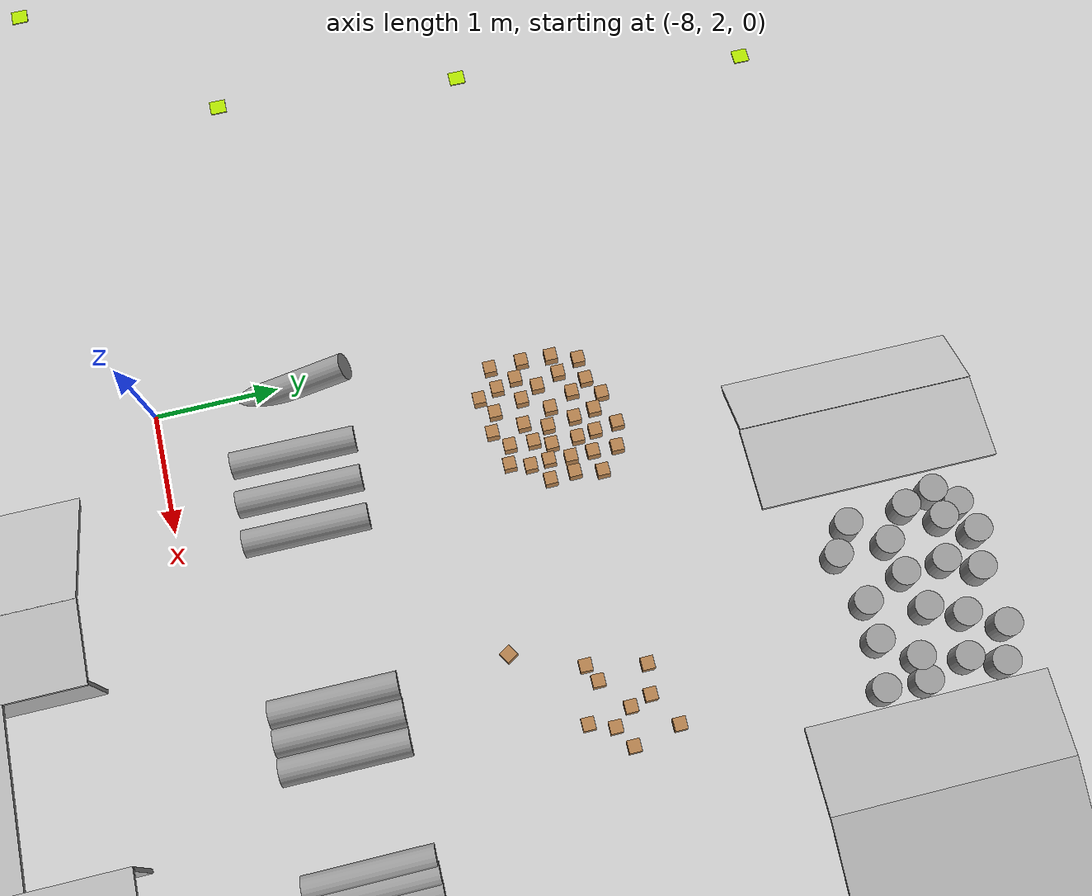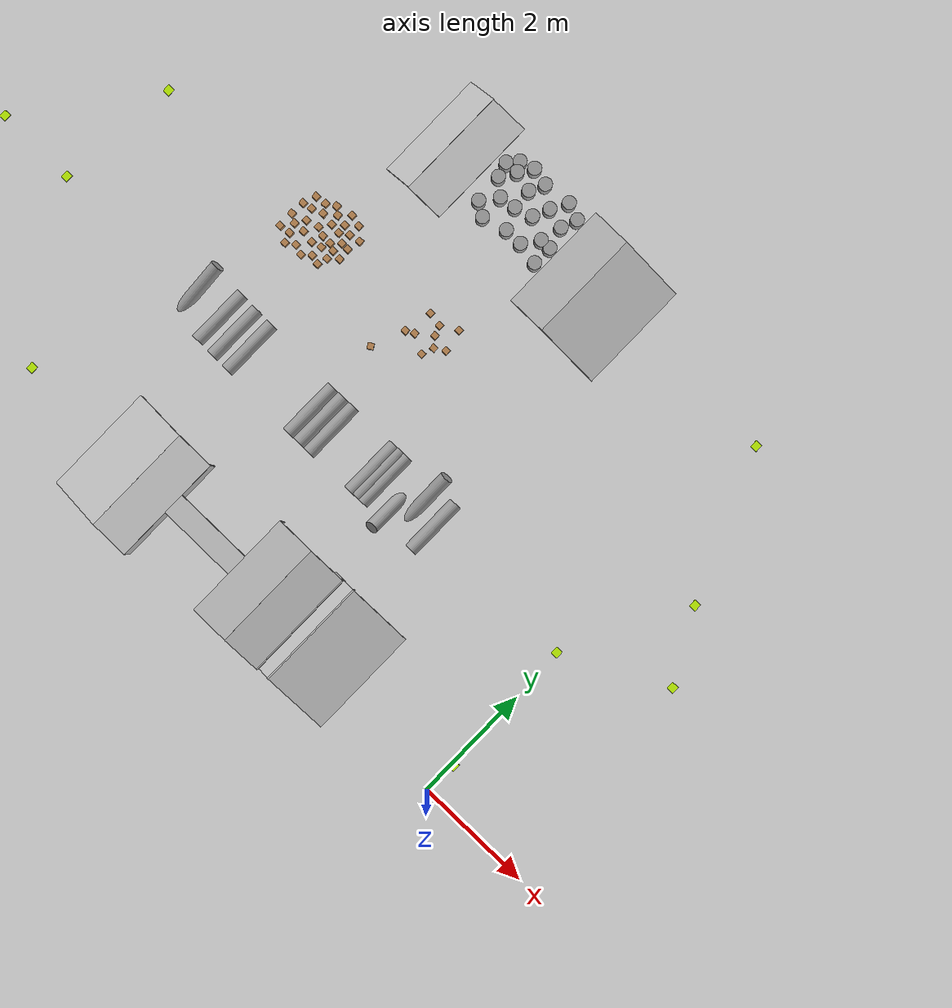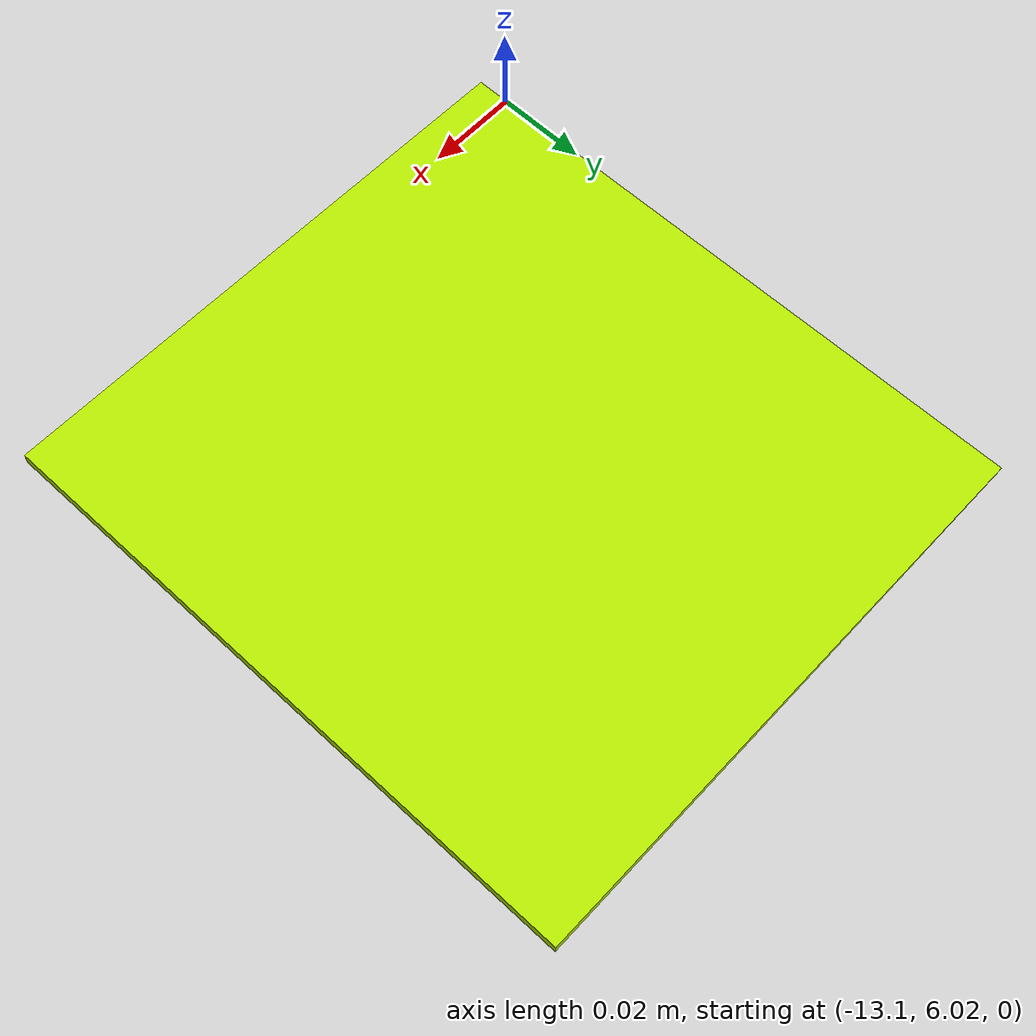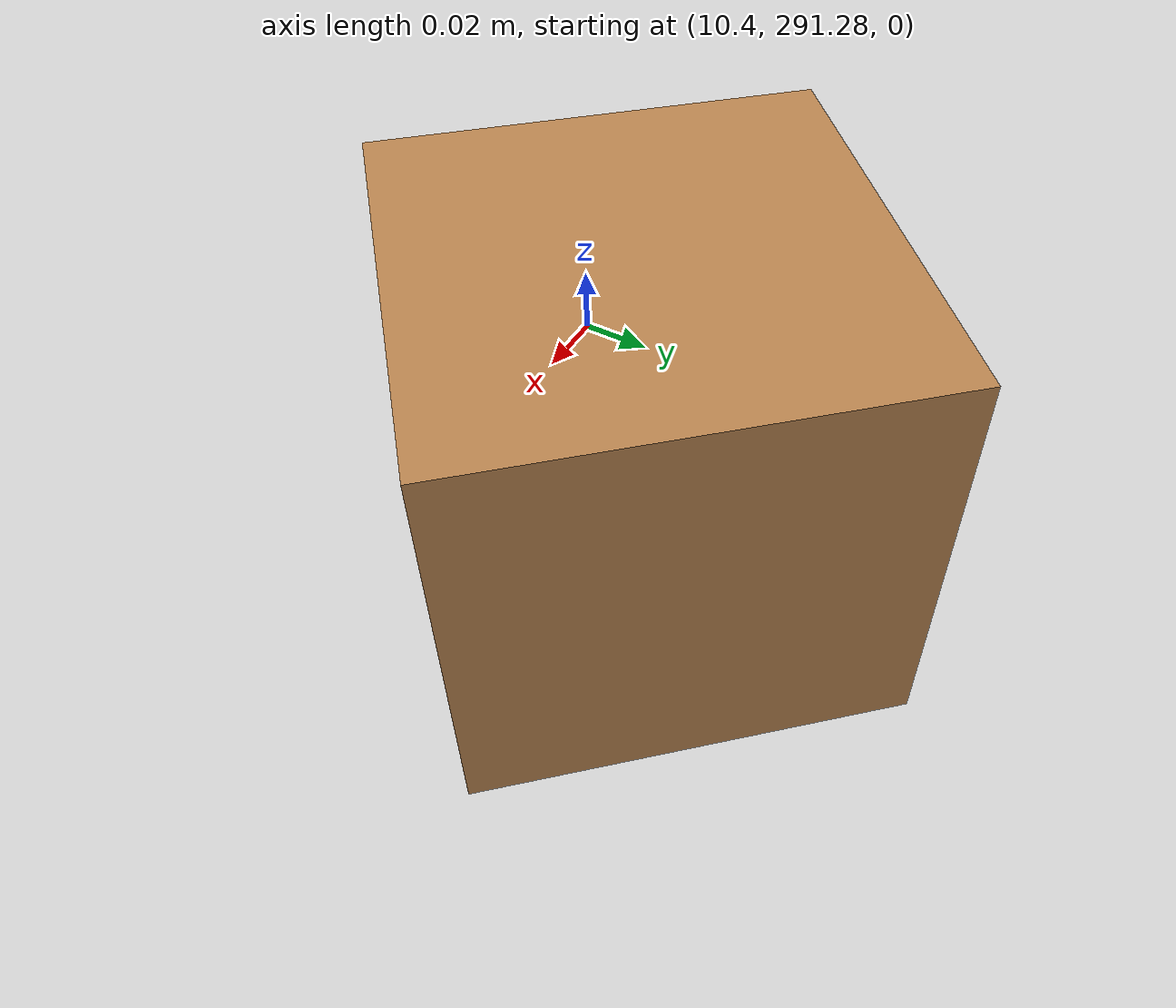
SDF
<sdf version="1.7">
 <world name="default">
  <model name="ground_plane">
   <static>1</static>
   <link name="link">
    <collision name="collision">
     <geometry><plane><normal>0 0 1</normal><size>100 100</size></plane></geometry>
     <surface>
      <contact><collide_bitmask>65535</collide_bitmask></contact>
      <friction><ode><mu>1.0</mu><mu2>1.0</mu2></ode></friction>
     </surface>
    </collision>
    <visual name="visual">
     <cast_shadows>0</cast_shadows>
     <geometry><plane><normal>0 0 1</normal><size>100 100</size></plane></geometry>
     <material>
      <script><uri>file://media/materials/scripts/gazebo.material</uri><name>Gazebo/Grey</name></script>
     </material>
    </visual>
   </link>
  </model>
  <light name="sun" type="directional">
   <pose>0 0 10 0 -0 0</pose>
   <diffuse>0.8 0.8 0.8 1</diffuse>
   <specular>0.2 0.2 0.2 1</specular>
   <attenuation>
    <range>1000</range>
    <constant>0.9</constant>
    <linear>0.01</linear>
    <quadratic>0.001</quadratic>
   </attenuation>
   <direction>-0.5 0.1 -0.9</direction>
   <spot><inner_angle>0</inner_angle><outer_angle>0</outer_angle><falloff>0</falloff></spot>
  </light>
  <gravity>0 0 -9.8</gravity>
  <magnetic_field>6e-06 2.3e-05 -4.2e-05</magnetic_field>
  <atmosphere type="adiabatic"/>
  <physics type="ode">
   <max_step_size>0.001</max_step_size>
   <real_time_factor>1</real_time_factor>
   <real_time_update_rate>1000</real_time_update_rate>
  </physics>
  <scene><ambient>0.4 0.4 0.4 1</ambient><background>0.7 0.7 0.7 1</background><shadows>1</shadows></scene>
  <spherical_coordinates>
   <surface_model>EARTH_WGS84</surface_model>
   <latitude_deg>0</latitude_deg>
   <longitude_deg>0</longitude_deg>
   <elevation>0</elevation>
   <heading_deg>0</heading_deg>
  </spherical_coordinates>
  <model name="box_clone">
   <static>1</static>
   <pose>-1.9971 0.496665 0 0 0.212574 0</pose>
   <link name="link">
    <collision name="collision"><geometry><box><size>1.99786 1.89779 0.0334761</size></box></geometry></collision>
    <visual name="visual"><geometry><box><size>1.99786 1.89779 0.0334761</size></box></geometry></visual>
   </link>
  </model>
  <model name="box_clone_clone">
   <static>1</static>
   <pose>-2.94544 0.495323 -0.771944 3.14159 -1.53604 3.14159</pose>
   <link name="link">
    <collision name="collision"><geometry><box><size>1.99786 1.89779 0.025973</size></box></geometry></collision>
    <visual name="visual"><geometry><box><size>1.99786 1.89779 0.025973</size></box></geometry></visual>
   </link>
  </model>
  <model name="box_clone_clone_0">
   <static>1</static>
   <pose>-3.28876 0.495679 0.025039 0 -0.548358 0</pose>
   <link name="link">
    <collision name="collision"><geometry><box><size>0.715653 1.89779 0.033476</size></box></geometry></collision>
    <visual name="visual"><geometry><box><size>0.715653 1.89779 0.033476</size></box></geometry></visual>
   </link>
  </model>
  <model name="box_clone_clone_0_clone">
   <static>1</static>
   <pose>-3.19988 0.495393 -0.032933 3.14159 -1.54205 3.14159</pose>
   <link name="link">
    <collision name="collision"><geometry><box><size>0.715654 1.89779 0.033476</size></box></geometry></collision>
    <visual name="visual"><geometry><box><size>0.715654 1.89779 0.033476</size></box></geometry></visual>
   </link>
  </model>
  <model name="box_clone_clone_1">
   <static>1</static>
   <pose>-3.54004 0.494466 0.379646 0 0.212574 0</pose>
   <link name="link">
    <collision name="collision"><geometry><box><size>0.666252 1.89779 0.033476</size></box></geometry></collision>
    <visual name="visual"><geometry><box><size>0.666252 1.89779 0.033476</size></box></geometry></visual>
   </link>
  </model>
  <model name="box_clone_clone_1_clone">
   <static>1</static>
   <pose>-4.19542 0.496691 0.444335 0 -0.017033 0</pose>
   <link name="link">
    <collision name="collision"><geometry><box><size>0.666252 1.89779 0.033476</size></box></geometry></collision>
    <visual name="visual"><geometry><box><size>0.666252 1.89779 0.033476</size></box></geometry></visual>
   </link>
  </model>
  <model name="box_clone_clone_1_clone_clone_0">
   <static>1</static>
   <pose>-4.50075 0.49442 0.117677 3.14159 -1.54109 3.14159</pose>
   <link name="link">
    <collision name="collision"><geometry><box><size>0.666252 1.89779 0.033476</size></box></geometry></collision>
    <visual name="visual"><geometry><box><size>0.666252 1.89779 0.033476</size></box></geometry></visual>
   </link>
  </model>
  <model name="box_clone_clone_1_clone_clone">
   <static>1</static>
   <pose>-5.19829 0.493755 0.426773 0 -0.017033 0</pose>
   <link name="link">
    <collision name="collision"><geometry><box><size>1.38712 0.374223 0.033476</size></box></geometry></collision>
    <visual name="visual"><geometry><box><size>1.38712 0.374223 0.033476</size></box></geometry></visual>
   </link>
  </model>
  <model name="box_clone_clone_1_clone_clone_1">
   <static>1</static>
   <pose>-6.21232 0.357872 0.409761 0 -0.017033 0</pose>
   <link name="link">
    <collision name="collision"><geometry><box><size>0.666252 1.89779 0.033476</size></box></geometry></collision>
    <visual name="visual"><geometry><box><size>0.666252 1.89779 0.033476</size></box></geometry></visual>
   </link>
  </model>
  <model name="box_clone_clone_2">
   <static>1</static>
   <pose>-7.44368 0.355255 -0.012815 0 -0.432808 0</pose>
   <link name="link">
    <collision name="collision"><geometry><box><size>1.99786 1.89779 0.033476</size></box></geometry></collision>
    <visual name="visual"><geometry><box><size>1.99786 1.89779 0.033476</size></box></geometry></visual>
   </link>
  </model>
  <model name="box_clone_clone_1_clone_clone_0_clone">
   <static>1</static>
   <pose>-5.88858 0.360109 0.090247 3.14159 -1.54109 3.14159</pose>
   <link name="link">
    <collision name="collision"><geometry><box><size>0.666252 1.89779 0.033476</size></box></geometry></collision>
    <visual name="visual"><geometry><box><size>0.666252 1.89779 0.033476</size></box></geometry></visual>
   </link>
  </model>
  <model name="unit_cylinder_clone_0">
   <link name="link">
    <inertial>
     <mass>0.0497635</mass>
     <inertia>
      <ixx>0.00430173</ixx>
      <ixy>0</ixy>
      <ixz>0</ixz>
      <iyy>0.00430173</iyy>
      <iyz>0</iyz>
      <izz>0.00030955</izz>
     </inertia>
    </inertial>
    <pose>0.001965 -0.009653 -0.499784 1.55252 -0 0</pose>
    <visual name="visual">
     <geometry><cylinder><radius>0.111539</radius><length>1</length></cylinder></geometry>
     <material>
      <script><name>Gazebo/Grey</name><uri>file://media/materials/scripts/gazebo.material</uri></script>
      <shader type="pixel"/>
     </material>
    </visual>
    <collision name="collision">
     <geometry><cylinder><radius>0.111539</radius><length>1</length></cylinder></geometry>
     <surface>
      <friction>
       <ode><mu>1.0</mu><mu2>1.0</mu2><fdir1>0 0 0</fdir1><slip1>0</slip1><slip2>0</slip2></ode>
       <torsional>
        <coefficient>1</coefficient>
        <patch_radius>0</patch_radius>
        <surface_radius>0</surface_radius>
        <use_patch_radius>1</use_patch_radius>
        <ode><slip>0</slip></ode>
       </torsional>
      </friction>
      <bounce><restitution_coefficient>0</restitution_coefficient><threshold>1e+06</threshold></bounce>
      <contact>
       <collide_without_contact>0</collide_without_contact>
       <collide_without_contact_bitmask>1</collide_without_contact_bitmask>
       <collide_bitmask>1</collide_bitmask>
       <ode>
        <soft_cfm>0</soft_cfm>
        <soft_erp>0.2</soft_erp>
        <kp>1e+13</kp>
        <kd>1</kd>
        <max_vel>0.01</max_vel>
        <min_depth>0</min_depth>
       </ode>
       <bullet>
        <split_impulse>1</split_impulse>
        <split_impulse_penetration_threshold>-0.01</split_impulse_penetration_threshold>
        <soft_cfm>0</soft_cfm>
        <soft_erp>0.2</soft_erp>
        <kp>1e+13</kp>
        <kd>1</kd>
       </bullet>
      </contact>
     </surface>
    </collision>
   </link>
   <static>1</static>
   <pose>-2.78057 3.00794 0.5 0 -0 0</pose>
  </model>
  <model name="unit_cylinder_clone_clone">
   <link name="link">
    <inertial>
     <mass>0.0497635</mass>
     <inertia>
      <ixx>0.00430173</ixx>
      <ixy>0</ixy>
      <ixz>0</ixz>
      <iyy>0.00430173</iyy>
      <iyz>0</iyz>
      <izz>0.00030955</izz>
     </inertia>
    </inertial>
    <pose>0.001965 -0.009653 -0.499784 1.55252 -0 0</pose>
    <visual name="visual">
     <geometry><cylinder><radius>0.111539</radius><length>1</length></cylinder></geometry>
     <material>
      <script><name>Gazebo/Grey</name><uri>file://media/materials/scripts/gazebo.material</uri></script>
      <shader type="pixel"/>
     </material>
    </visual>
    <collision name="collision">
     <geometry><cylinder><radius>0.111539</radius><length>1</length></cylinder></geometry>
     <surface>
      <friction>
       <ode><mu>1.0</mu><mu2>1.0</mu2><fdir1>0 0 0</fdir1><slip1>0</slip1><slip2>0</slip2></ode>
       <torsional>
        <coefficient>1</coefficient>
        <patch_radius>0</patch_radius>
        <surface_radius>0</surface_radius>
        <use_patch_radius>1</use_patch_radius>
        <ode><slip>0</slip></ode>
       </torsional>
      </friction>
      <bounce><restitution_coefficient>0</restitution_coefficient><threshold>1e+06</threshold></bounce>
      <contact>
       <collide_without_contact>0</collide_without_contact>
       <collide_without_contact_bitmask>1</collide_without_contact_bitmask>
       <collide_bitmask>1</collide_bitmask>
       <ode>
        <soft_cfm>0</soft_cfm>
        <soft_erp>0.2</soft_erp>
        <kp>1e+13</kp>
        <kd>1</kd>
        <max_vel>0.01</max_vel>
        <min_depth>0</min_depth>
       </ode>
       <bullet>
        <split_impulse>1</split_impulse>
        <split_impulse_penetration_threshold>-0.01</split_impulse_penetration_threshold>
        <soft_cfm>0</soft_cfm>
        <soft_erp>0.2</soft_erp>
        <kp>1e+13</kp>
        <kd>1</kd>
       </bullet>
      </contact>
     </surface>
    </collision>
   </link>
   <static>1</static>
   <pose>-3.16214 3.06519 0.5 0.34698 -0 0</pose>
  </model>
  <model name="unit_cylinder_clone_clone_clone">
   <link name="link">
    <inertial>
     <mass>0.0497635</mass>
     <inertia>
      <ixx>0.00430173</ixx>
      <ixy>0</ixy>
      <ixz>0</ixz>
      <iyy>0.00430173</iyy>
      <iyz>0</iyz>
      <izz>0.00030955</izz>
     </inertia>
    </inertial>
    <pose>0.001965 -0.009653 -0.499784 1.55252 -0 0</pose>
    <visual name="visual">
     <geometry><cylinder><radius>0.111539</radius><length>1</length></cylinder></geometry>
     <material>
      <script><name>Gazebo/Grey</name><uri>file://media/materials/scripts/gazebo.material</uri></script>
      <shader type="pixel"/>
     </material>
    </visual>
    <collision name="collision">
     <geometry><cylinder><radius>0.111539</radius><length>1</length></cylinder></geometry>
     <surface>
      <friction>
       <ode><mu>1.0</mu><mu2>1.0</mu2><fdir1>0 0 0</fdir1><slip1>0</slip1><slip2>0</slip2></ode>
       <torsional>
        <coefficient>1</coefficient>
        <patch_radius>0</patch_radius>
        <surface_radius>0</surface_radius>
        <use_patch_radius>1</use_patch_radius>
        <ode><slip>0</slip></ode>
       </torsional>
      </friction>
      <bounce><restitution_coefficient>0</restitution_coefficient><threshold>1e+06</threshold></bounce>
      <contact>
       <collide_without_contact>0</collide_without_contact>
       <collide_without_contact_bitmask>1</collide_without_contact_bitmask>
       <collide_bitmask>1</collide_bitmask>
       <ode>
        <soft_cfm>0</soft_cfm>
        <soft_erp>0.2</soft_erp>
        <kp>1e+13</kp>
        <kd>1</kd>
        <max_vel>0.01</max_vel>
        <min_depth>0</min_depth>
       </ode>
       <bullet>
        <split_impulse>1</split_impulse>
        <split_impulse_penetration_threshold>-0.01</split_impulse_penetration_threshold>
        <soft_cfm>0</soft_cfm>
        <soft_erp>0.2</soft_erp>
        <kp>1e+13</kp>
        <kd>1</kd>
       </bullet>
      </contact>
     </surface>
    </collision>
   </link>
   <static>1</static>
   <pose>-3.45585 3.01997 0.46206 -0.51125 0 0</pose>
  </model>
  <model name="unit_cylinder_clone_1">
   <link name="link">
    <inertial>
     <mass>0.0497635</mass>
     <inertia>
      <ixx>0.00430173</ixx>
      <ixy>0</ixy>
      <ixz>0</ixz>
      <iyy>0.00430173</iyy>
      <iyz>0</iyz>
      <izz>0.00030955</izz>
     </inertia>
    </inertial>
    <pose>0.001965 -0.009653 -0.499784 1.55252 -0 0</pose>
    <visual name="visual">
     <geometry><cylinder><radius>0.111539</radius><length>1</length></cylinder></geometry>
     <material>
      <script><name>Gazebo/Grey</name><uri>file://media/materials/scripts/gazebo.material</uri></script>
      <shader type="pixel"/>
     </material>
    </visual>
    <collision name="collision">
     <geometry><cylinder><radius>0.111539</radius><length>1</length></cylinder></geometry>
     <surface>
      <friction>
       <ode><mu>1.0</mu><mu2>1.0</mu2><fdir1>0 0 0</fdir1><slip1>0</slip1><slip2>0</slip2></ode>
       <torsional>
        <coefficient>1</coefficient>
        <patch_radius>0</patch_radius>
        <surface_radius>0</surface_radius>
        <use_patch_radius>1</use_patch_radius>
        <ode><slip>0</slip></ode>
       </torsional>
      </friction>
      <bounce><restitution_coefficient>0</restitution_coefficient><threshold>1e+06</threshold></bounce>
      <contact>
       <collide_without_contact>0</collide_without_contact>
       <collide_without_contact_bitmask>1</collide_without_contact_bitmask>
       <collide_bitmask>1</collide_bitmask>
       <ode>
        <soft_cfm>0</soft_cfm>
        <soft_erp>0.2</soft_erp>
        <kp>1e+13</kp>
        <kd>1</kd>
        <max_vel>0.01</max_vel>
        <min_depth>0</min_depth>
       </ode>
       <bullet>
        <split_impulse>1</split_impulse>
        <split_impulse_penetration_threshold>-0.01</split_impulse_penetration_threshold>
        <soft_cfm>0</soft_cfm>
        <soft_erp>0.2</soft_erp>
        <kp>1e+13</kp>
        <kd>1</kd>
       </bullet>
      </contact>
     </surface>
    </collision>
   </link>
   <static>1</static>
   <pose>-3.83638 3.01167 0.5 0 -0 0</pose>
  </model>
  <model name="unit_cylinder_clone_2">
   <link name="link">
    <inertial>
     <mass>0.0497635</mass>
     <inertia>
      <ixx>0.00430173</ixx>
      <ixy>0</ixy>
      <ixz>0</ixz>
      <iyy>0.00430173</iyy>
      <iyz>0</iyz>
      <izz>0.00030955</izz>
     </inertia>
    </inertial>
    <pose>0.001965 -0.009653 -0.499784 1.55252 -0 0</pose>
    <visual name="visual">
     <geometry><cylinder><radius>0.111539</radius><length>1</length></cylinder></geometry>
     <material>
      <script><name>Gazebo/Grey</name><uri>file://media/materials/scripts/gazebo.material</uri></script>
      <shader type="pixel"/>
     </material>
    </visual>
    <collision name="collision">
     <geometry><cylinder><radius>0.111539</radius><length>1</length></cylinder></geometry>
     <surface>
      <friction>
       <ode><mu>1.0</mu><mu2>1.0</mu2><fdir1>0 0 0</fdir1><slip1>0</slip1><slip2>0</slip2></ode>
       <torsional>
        <coefficient>1</coefficient>
        <patch_radius>0</patch_radius>
        <surface_radius>0</surface_radius>
        <use_patch_radius>1</use_patch_radius>
        <ode><slip>0</slip></ode>
       </torsional>
      </friction>
      <bounce><restitution_coefficient>0</restitution_coefficient><threshold>1e+06</threshold></bounce>
      <contact>
       <collide_without_contact>0</collide_without_contact>
       <collide_without_contact_bitmask>1</collide_without_contact_bitmask>
       <collide_bitmask>1</collide_bitmask>
       <ode>
        <soft_cfm>0</soft_cfm>
        <soft_erp>0.2</soft_erp>
        <kp>1e+13</kp>
        <kd>1</kd>
        <max_vel>0.01</max_vel>
        <min_depth>0</min_depth>
       </ode>
       <bullet>
        <split_impulse>1</split_impulse>
        <split_impulse_penetration_threshold>-0.01</split_impulse_penetration_threshold>
        <soft_cfm>0</soft_cfm>
        <soft_erp>0.2</soft_erp>
        <kp>1e+13</kp>
        <kd>1</kd>
       </bullet>
      </contact>
     </surface>
    </collision>
   </link>
   <static>1</static>
   <pose>-3.96673 3.01014 0.5 0 -0 0</pose>
  </model>
  <model name="unit_cylinder_clone_3">
   <link name="link">
    <inertial>
     <mass>0.0497635</mass>
     <inertia>
      <ixx>0.00430173</ixx>
      <ixy>0</ixy>
      <ixz>0</ixz>
      <iyy>0.00430173</iyy>
      <iyz>0</iyz>
      <izz>0.00030955</izz>
     </inertia>
    </inertial>
    <pose>0.001965 -0.009653 -0.499784 1.55252 -0 0</pose>
    <visual name="visual">
     <geometry><cylinder><radius>0.111539</radius><length>1</length></cylinder></geometry>
     <material>
      <script><name>Gazebo/Grey</name><uri>file://media/materials/scripts/gazebo.material</uri></script>
      <shader type="pixel"/>
     </material>
    </visual>
    <collision name="collision">
     <geometry><cylinder><radius>0.111539</radius><length>1</length></cylinder></geometry>
     <surface>
      <friction>
       <ode><mu>1.0</mu><mu2>1.0</mu2><fdir1>0 0 0</fdir1><slip1>0</slip1><slip2>0</slip2></ode>
       <torsional>
        <coefficient>1</coefficient>
        <patch_radius>0</patch_radius>
        <surface_radius>0</surface_radius>
        <use_patch_radius>1</use_patch_radius>
        <ode><slip>0</slip></ode>
       </torsional>
      </friction>
      <bounce><restitution_coefficient>0</restitution_coefficient><threshold>1e+06</threshold></bounce>
      <contact>
       <collide_without_contact>0</collide_without_contact>
       <collide_without_contact_bitmask>1</collide_without_contact_bitmask>
       <collide_bitmask>1</collide_bitmask>
       <ode>
        <soft_cfm>0</soft_cfm>
        <soft_erp>0.2</soft_erp>
        <kp>1e+13</kp>
        <kd>1</kd>
        <max_vel>0.01</max_vel>
        <min_depth>0</min_depth>
       </ode>
       <bullet>
        <split_impulse>1</split_impulse>
        <split_impulse_penetration_threshold>-0.01</split_impulse_penetration_threshold>
        <soft_cfm>0</soft_cfm>
        <soft_erp>0.2</soft_erp>
        <kp>1e+13</kp>
        <kd>1</kd>
       </bullet>
      </contact>
     </surface>
    </collision>
   </link>
   <static>1</static>
   <pose>-4.09699 3.00429 0.5 0 -0 0</pose>
  </model>
  <model name="unit_cylinder_clone_4">
   <link name="link">
    <inertial>
     <mass>0.0497635</mass>
     <inertia>
      <ixx>0.00430173</ixx>
      <ixy>0</ixy>
      <ixz>0</ixz>
      <iyy>0.00430173</iyy>
      <iyz>0</iyz>
      <izz>0.00030955</izz>
     </inertia>
    </inertial>
    <pose>0.001965 -0.009653 -0.499784 1.55252 -0 0</pose>
    <visual name="visual">
     <geometry><cylinder><radius>0.111539</radius><length>1</length></cylinder></geometry>
     <material>
      <script><name>Gazebo/Grey</name><uri>file://media/materials/scripts/gazebo.material</uri></script>
      <shader type="pixel"/>
     </material>
    </visual>
    <collision name="collision">
     <geometry><cylinder><radius>0.111539</radius><length>1</length></cylinder></geometry>
     <surface>
      <friction>
       <ode><mu>1.0</mu><mu2>1.0</mu2><fdir1>0 0 0</fdir1><slip1>0</slip1><slip2>0</slip2></ode>
       <torsional>
        <coefficient>1</coefficient>
        <patch_radius>0</patch_radius>
        <surface_radius>0</surface_radius>
        <use_patch_radius>1</use_patch_radius>
        <ode><slip>0</slip></ode>
       </torsional>
      </friction>
      <bounce><restitution_coefficient>0</restitution_coefficient><threshold>1e+06</threshold></bounce>
      <contact>
       <collide_without_contact>0</collide_without_contact>
       <collide_without_contact_bitmask>1</collide_without_contact_bitmask>
       <collide_bitmask>1</collide_bitmask>
       <ode>
        <soft_cfm>0</soft_cfm>
        <soft_erp>0.2</soft_erp>
        <kp>1e+13</kp>
        <kd>1</kd>
        <max_vel>0.01</max_vel>
        <min_depth>0</min_depth>
       </ode>
       <bullet>
        <split_impulse>1</split_impulse>
        <split_impulse_penetration_threshold>-0.01</split_impulse_penetration_threshold>
        <soft_cfm>0</soft_cfm>
        <soft_erp>0.2</soft_erp>
        <kp>1e+13</kp>
        <kd>1</kd>
       </bullet>
      </contact>
     </surface>
    </collision>
   </link>
   <static>1</static>
   <pose>-4.97391 2.99072 0.5 0 -0 0</pose>
  </model>
  <model name="unit_cylinder_clone_5">
   <link name="link">
    <inertial>
     <mass>0.0497635</mass>
     <inertia>
      <ixx>0.00430173</ixx>
      <ixy>0</ixy>
      <ixz>0</ixz>
      <iyy>0.00430173</iyy>
      <iyz>0</iyz>
      <izz>0.00030955</izz>
     </inertia>
    </inertial>
    <pose>0.001965 -0.009653 -0.499784 1.55252 -0 0</pose>
    <visual name="visual">
     <geometry><cylinder><radius>0.111539</radius><length>1</length></cylinder></geometry>
     <material>
      <script><name>Gazebo/Grey</name><uri>file://media/materials/scripts/gazebo.material</uri></script>
      <shader type="pixel"/>
     </material>
    </visual>
    <collision name="collision">
     <geometry><cylinder><radius>0.111539</radius><length>1</length></cylinder></geometry>
     <surface>
      <friction>
       <ode><mu>1.0</mu><mu2>1.0</mu2><fdir1>0 0 0</fdir1><slip1>0</slip1><slip2>0</slip2></ode>
       <torsional>
        <coefficient>1</coefficient>
        <patch_radius>0</patch_radius>
        <surface_radius>0</surface_radius>
        <use_patch_radius>1</use_patch_radius>
        <ode><slip>0</slip></ode>
       </torsional>
      </friction>
      <bounce><restitution_coefficient>0</restitution_coefficient><threshold>1e+06</threshold></bounce>
      <contact>
       <collide_without_contact>0</collide_without_contact>
       <collide_without_contact_bitmask>1</collide_without_contact_bitmask>
       <collide_bitmask>1</collide_bitmask>
       <ode>
        <soft_cfm>0</soft_cfm>
        <soft_erp>0.2</soft_erp>
        <kp>1e+13</kp>
        <kd>1</kd>
        <max_vel>0.01</max_vel>
        <min_depth>0</min_depth>
       </ode>
       <bullet>
        <split_impulse>1</split_impulse>
        <split_impulse_penetration_threshold>-0.01</split_impulse_penetration_threshold>
        <soft_cfm>0</soft_cfm>
        <soft_erp>0.2</soft_erp>
        <kp>1e+13</kp>
        <kd>1</kd>
       </bullet>
      </contact>
     </surface>
    </collision>
   </link>
   <static>1</static>
   <pose>-5.19562 2.98929 0.5 0 -0 0</pose>
  </model>
  <model name="unit_cylinder_clone_6">
   <link name="link">
    <inertial>
     <mass>0.0497635</mass>
     <inertia>
      <ixx>0.00430173</ixx>
      <ixy>0</ixy>
      <ixz>0</ixz>
      <iyy>0.00430173</iyy>
      <iyz>0</iyz>
      <izz>0.00030955</izz>
     </inertia>
    </inertial>
    <pose>0.001965 -0.009653 -0.499784 1.55252 -0 0</pose>
    <visual name="visual">
     <geometry><cylinder><radius>0.111539</radius><length>1</length></cylinder></geometry>
     <material>
      <script><name>Gazebo/Grey</name><uri>file://media/materials/scripts/gazebo.material</uri></script>
      <shader type="pixel"/>
     </material>
    </visual>
    <collision name="collision">
     <geometry><cylinder><radius>0.111539</radius><length>1</length></cylinder></geometry>
     <surface>
      <friction>
       <ode><mu>1.0</mu><mu2>1.0</mu2><fdir1>0 0 0</fdir1><slip1>0</slip1><slip2>0</slip2></ode>
       <torsional>
        <coefficient>1</coefficient>
        <patch_radius>0</patch_radius>
        <surface_radius>0</surface_radius>
        <use_patch_radius>1</use_patch_radius>
        <ode><slip>0</slip></ode>
       </torsional>
      </friction>
      <bounce><restitution_coefficient>0</restitution_coefficient><threshold>1e+06</threshold></bounce>
      <contact>
       <collide_without_contact>0</collide_without_contact>
       <collide_without_contact_bitmask>1</collide_without_contact_bitmask>
       <collide_bitmask>1</collide_bitmask>
       <ode>
        <soft_cfm>0</soft_cfm>
        <soft_erp>0.2</soft_erp>
        <kp>1e+13</kp>
        <kd>1</kd>
        <max_vel>0.01</max_vel>
        <min_depth>0</min_depth>
       </ode>
       <bullet>
        <split_impulse>1</split_impulse>
        <split_impulse_penetration_threshold>-0.01</split_impulse_penetration_threshold>
        <soft_cfm>0</soft_cfm>
        <soft_erp>0.2</soft_erp>
        <kp>1e+13</kp>
        <kd>1</kd>
       </bullet>
      </contact>
     </surface>
    </collision>
   </link>
   <static>1</static>
   <pose>-5.41624 2.98556 0.5 0 -0 0</pose>
  </model>
  <model name="unit_cylinder_clone_7">
   <link name="link">
    <inertial>
     <mass>0.0497635</mass>
     <inertia>
      <ixx>0.00430173</ixx>
      <ixy>0</ixy>
      <ixz>0</ixz>
      <iyy>0.00430173</iyy>
      <iyz>0</iyz>
      <izz>0.00030955</izz>
     </inertia>
    </inertial>
    <pose>0.001965 -0.009653 -0.499784 1.55252 -0 0</pose>
    <visual name="visual">
     <geometry><cylinder><radius>0.111539</radius><length>1</length></cylinder></geometry>
     <material>
      <script><name>Gazebo/Grey</name><uri>file://media/materials/scripts/gazebo.material</uri></script>
      <shader type="pixel"/>
     </material>
    </visual>
    <collision name="collision">
     <geometry><cylinder><radius>0.111539</radius><length>1</length></cylinder></geometry>
     <surface>
      <friction>
       <ode><mu>1.0</mu><mu2>1.0</mu2><fdir1>0 0 0</fdir1><slip1>0</slip1><slip2>0</slip2></ode>
       <torsional>
        <coefficient>1</coefficient>
        <patch_radius>0</patch_radius>
        <surface_radius>0</surface_radius>
        <use_patch_radius>1</use_patch_radius>
        <ode><slip>0</slip></ode>
       </torsional>
      </friction>
      <bounce><restitution_coefficient>0</restitution_coefficient><threshold>1e+06</threshold></bounce>
      <contact>
       <collide_without_contact>0</collide_without_contact>
       <collide_without_contact_bitmask>1</collide_without_contact_bitmask>
       <collide_bitmask>1</collide_bitmask>
       <ode>
        <soft_cfm>0</soft_cfm>
        <soft_erp>0.2</soft_erp>
        <kp>1e+13</kp>
        <kd>1</kd>
        <max_vel>0.01</max_vel>
        <min_depth>0</min_depth>
       </ode>
       <bullet>
        <split_impulse>1</split_impulse>
        <split_impulse_penetration_threshold>-0.01</split_impulse_penetration_threshold>
        <soft_cfm>0</soft_cfm>
        <soft_erp>0.2</soft_erp>
        <kp>1e+13</kp>
        <kd>1</kd>
       </bullet>
      </contact>
     </surface>
    </collision>
   </link>
   <static>1</static>
   <pose>-6.78289 3.02429 0.5 0 -0 0</pose>
  </model>
  <model name="unit_cylinder_clone_8">
   <link name="link">
    <inertial>
     <mass>0.0497635</mass>
     <inertia>
      <ixx>0.00430173</ixx>
      <ixy>0</ixy>
      <ixz>0</ixz>
      <iyy>0.00430173</iyy>
      <iyz>0</iyz>
      <izz>0.00030955</izz>
     </inertia>
    </inertial>
    <pose>0.001965 -0.009653 -0.499784 1.55252 -0 0</pose>
    <visual name="visual">
     <geometry><cylinder><radius>0.111539</radius><length>1</length></cylinder></geometry>
     <material>
      <script><name>Gazebo/Grey</name><uri>file://media/materials/scripts/gazebo.material</uri></script>
      <shader type="pixel"/>
     </material>
    </visual>
    <collision name="collision">
     <geometry><cylinder><radius>0.111539</radius><length>1</length></cylinder></geometry>
     <surface>
      <friction>
       <ode><mu>1.0</mu><mu2>1.0</mu2><fdir1>0 0 0</fdir1><slip1>0</slip1><slip2>0</slip2></ode>
       <torsional>
        <coefficient>1</coefficient>
        <patch_radius>0</patch_radius>
        <surface_radius>0</surface_radius>
        <use_patch_radius>1</use_patch_radius>
        <ode><slip>0</slip></ode>
       </torsional>
      </friction>
      <bounce><restitution_coefficient>0</restitution_coefficient><threshold>1e+06</threshold></bounce>
      <contact>
       <collide_without_contact>0</collide_without_contact>
       <collide_without_contact_bitmask>1</collide_without_contact_bitmask>
       <collide_bitmask>1</collide_bitmask>
       <ode>
        <soft_cfm>0</soft_cfm>
        <soft_erp>0.2</soft_erp>
        <kp>1e+13</kp>
        <kd>1</kd>
        <max_vel>0.01</max_vel>
        <min_depth>0</min_depth>
       </ode>
       <bullet>
        <split_impulse>1</split_impulse>
        <split_impulse_penetration_threshold>-0.01</split_impulse_penetration_threshold>
        <soft_cfm>0</soft_cfm>
        <soft_erp>0.2</soft_erp>
        <kp>1e+13</kp>
        <kd>1</kd>
       </bullet>
      </contact>
     </surface>
    </collision>
   </link>
   <static>1</static>
   <pose>-7.10923 3.03145 0.5 0 -0 0</pose>
  </model>
  <model name="unit_cylinder_clone_9">
   <link name="link">
    <inertial>
     <mass>0.0497635</mass>
     <inertia>
      <ixx>0.00430173</ixx>
      <ixy>0</ixy>
      <ixz>0</ixz>
      <iyy>0.00430173</iyy>
      <iyz>0</iyz>
      <izz>0.00030955</izz>
     </inertia>
    </inertial>
    <pose>0.001965 -0.009653 -0.499784 1.55252 -0 0</pose>
    <visual name="visual">
     <geometry><cylinder><radius>0.111539</radius><length>1</length></cylinder></geometry>
     <material>
      <script><name>Gazebo/Grey</name><uri>file://media/materials/scripts/gazebo.material</uri></script>
      <shader type="pixel"/>
     </material>
    </visual>
    <collision name="collision">
     <geometry><cylinder><radius>0.111539</radius><length>1</length></cylinder></geometry>
     <surface>
      <friction>
       <ode><mu>1.0</mu><mu2>1.0</mu2><fdir1>0 0 0</fdir1><slip1>0</slip1><slip2>0</slip2></ode>
       <torsional>
        <coefficient>1</coefficient>
        <patch_radius>0</patch_radius>
        <surface_radius>0</surface_radius>
        <use_patch_radius>1</use_patch_radius>
        <ode><slip>0</slip></ode>
       </torsional>
      </friction>
      <bounce><restitution_coefficient>0</restitution_coefficient><threshold>1e+06</threshold></bounce>
      <contact>
       <collide_without_contact>0</collide_without_contact>
       <collide_without_contact_bitmask>1</collide_without_contact_bitmask>
       <collide_bitmask>1</collide_bitmask>
       <ode>
        <soft_cfm>0</soft_cfm>
        <soft_erp>0.2</soft_erp>
        <kp>1e+13</kp>
        <kd>1</kd>
        <max_vel>0.01</max_vel>
        <min_depth>0</min_depth>
       </ode>
       <bullet>
        <split_impulse>1</split_impulse>
        <split_impulse_penetration_threshold>-0.01</split_impulse_penetration_threshold>
        <soft_cfm>0</soft_cfm>
        <soft_erp>0.2</soft_erp>
        <kp>1e+13</kp>
        <kd>1</kd>
       </bullet>
      </contact>
     </surface>
    </collision>
   </link>
   <static>1</static>
   <pose>-7.44013 3.04124 0.5 0 -0 0</pose>
  </model>
  <model name="unit_cylinder_clone_clone_clone_0">
   <link name="link">
    <inertial>
     <mass>0.0497635</mass>
     <inertia>
      <ixx>0.00430173</ixx>
      <ixy>0</ixy>
      <ixz>0</ixz>
      <iyy>0.00430173</iyy>
      <iyz>0</iyz>
      <izz>0.00030955</izz>
     </inertia>
    </inertial>
    <pose>0.001965 -0.009653 -0.499784 1.55252 -0 0</pose>
    <visual name="visual">
     <geometry><cylinder><radius>0.111539</radius><length>1</length></cylinder></geometry>
     <material>
      <script><name>Gazebo/Grey</name><uri>file://media/materials/scripts/gazebo.material</uri></script>
      <shader type="pixel"/>
     </material>
    </visual>
    <collision name="collision">
     <geometry><cylinder><radius>0.111539</radius><length>1</length></cylinder></geometry>
     <surface>
      <friction>
       <ode><mu>1.0</mu><mu2>1.0</mu2><fdir1>0 0 0</fdir1><slip1>0</slip1><slip2>0</slip2></ode>
       <torsional>
        <coefficient>1</coefficient>
        <patch_radius>0</patch_radius>
        <surface_radius>0</surface_radius>
        <use_patch_radius>1</use_patch_radius>
        <ode><slip>0</slip></ode>
       </torsional>
      </friction>
      <bounce><restitution_coefficient>0</restitution_coefficient><threshold>1e+06</threshold></bounce>
      <contact>
       <collide_without_contact>0</collide_without_contact>
       <collide_without_contact_bitmask>1</collide_without_contact_bitmask>
       <collide_bitmask>1</collide_bitmask>
       <ode>
        <soft_cfm>0</soft_cfm>
        <soft_erp>0.2</soft_erp>
        <kp>1e+13</kp>
        <kd>1</kd>
        <max_vel>0.01</max_vel>
        <min_depth>0</min_depth>
       </ode>
       <bullet>
        <split_impulse>1</split_impulse>
        <split_impulse_penetration_threshold>-0.01</split_impulse_penetration_threshold>
        <soft_cfm>0</soft_cfm>
        <soft_erp>0.2</soft_erp>
        <kp>1e+13</kp>
        <kd>1</kd>
       </bullet>
      </contact>
     </surface>
    </collision>
   </link>
   <static>1</static>
   <pose>-7.99139 2.9479 0.5 0.34698 -0 0</pose>
  </model>
  <model name="box_clone_clone_3">
   <static>1</static>
   <pose>-2.71446 7.30395 0 0 0.212574 0</pose>
   <link name="link">
    <collision name="collision"><geometry><box><size>1.99786 1.89779 0.033476</size></box></geometry></collision>
    <visual name="visual"><geometry><box><size>1.99786 1.89779 0.033476</size></box></geometry></visual>
   </link>
  </model>
  <model name="wood_cube_10cm">
   <link name="link">
    <pose>0 0 0.05 0 -0 0</pose>
    <inertial>
     <mass>0.5167</mass>
     <inertia>
      <ixx>0.000861167</ixx>
      <ixy>0</ixy>
      <ixz>0</ixz>
      <iyy>0.000861167</iyy>
      <iyz>0</iyz>
      <izz>0.000861167</izz>
     </inertia>
    </inertial>
    <collision name="collision">
     <geometry><box><size>0.1 0.1 0.1</size></box></geometry>
     <surface>
      <contact>
       <poissons_ratio>0.347</poissons_ratio>
       <elastic_modulus>8.8e+09</elastic_modulus>
       <ode><kp>100000</kp><kd>100</kd><max_vel>100</max_vel><min_depth>0.001</min_depth></ode>
      </contact>
      <friction>
       <torsional>
        <coefficient>1</coefficient>
        <use_patch_radius>0</use_patch_radius>
        <surface_radius>0.01</surface_radius>
       </torsional>
      </friction>
     </surface>
    </collision>
    <visual name="visual">
     <geometry><box><size>0.1 0.1 0.1</size></box></geometry>
     <material>
      <script><uri>file://media/materials/scripts/gazebo.material</uri><name>Gazebo/Wood</name></script>
     </material>
    </visual>
   </link>
   <pose>-4.5337 5.10533 -0.001013 0 -0 0</pose>
  </model>
  <model name="wood_cube_10cm_clone">
   <link name="link">
    <pose>0 0 0.05 0 -0 0</pose>
    <inertial>
     <mass>0.5167</mass>
     <inertia>
      <ixx>0.000861167</ixx>
      <ixy>0</ixy>
      <ixz>0</ixz>
      <iyy>0.000861167</iyy>
      <iyz>0</iyz>
      <izz>0.000861167</izz>
     </inertia>
    </inertial>
    <collision name="collision">
     <geometry><box><size>0.1 0.1 0.1</size></box></geometry>
     <surface>
      <contact>
       <poissons_ratio>0.347</poissons_ratio>
       <elastic_modulus>8.8e+09</elastic_modulus>
       <ode><kp>100000</kp><kd>100</kd><max_vel>100</max_vel><min_depth>0.001</min_depth></ode>
      </contact>
      <friction>
       <torsional>
        <coefficient>1</coefficient>
        <use_patch_radius>0</use_patch_radius>
        <surface_radius>0.01</surface_radius>
       </torsional>
      </friction>
     </surface>
    </collision>
    <visual name="visual">
     <geometry><box><size>0.1 0.1 0.1</size></box></geometry>
     <material>
      <script><uri>file://media/materials/scripts/gazebo.material</uri><name>Gazebo/Wood</name></script>
     </material>
    </visual>
   </link>
   <pose>-4.77393 4.80973 -0.001013 0 -0 0</pose>
  </model>
  <model name="wood_cube_10cm_clone_0">
   <link name="link">
    <pose>0 0 0.05 0 -0 0</pose>
    <inertial>
     <mass>0.5167</mass>
     <inertia>
      <ixx>0.000861167</ixx>
      <ixy>0</ixy>
      <ixz>0</ixz>
      <iyy>0.000861167</iyy>
      <iyz>0</iyz>
      <izz>0.000861167</izz>
     </inertia>
    </inertial>
    <collision name="collision">
     <geometry><box><size>0.1 0.1 0.1</size></box></geometry>
     <surface>
      <contact>
       <poissons_ratio>0.347</poissons_ratio>
       <elastic_modulus>8.8e+09</elastic_modulus>
       <ode><kp>100000</kp><kd>100</kd><max_vel>100</max_vel><min_depth>0.001</min_depth></ode>
      </contact>
      <friction>
       <torsional>
        <coefficient>1</coefficient>
        <use_patch_radius>0</use_patch_radius>
        <surface_radius>0.01</surface_radius>
       </torsional>
      </friction>
     </surface>
    </collision>
    <visual name="visual">
     <geometry><box><size>0.1 0.1 0.1</size></box></geometry>
     <material>
      <script><uri>file://media/materials/scripts/gazebo.material</uri><name>Gazebo/Wood</name></script>
     </material>
    </visual>
   </link>
   <pose>-4.82741 5.1542 -0.001013 0 -0 0</pose>
  </model>
  <model name="wood_cube_10cm_clone_1">
   <link name="link">
    <pose>0 0 0.05 0 -0 0</pose>
    <inertial>
     <mass>0.5167</mass>
     <inertia>
      <ixx>0.000861167</ixx>
      <ixy>0</ixy>
      <ixz>0</ixz>
      <iyy>0.000861167</iyy>
      <iyz>0</iyz>
      <izz>0.000861167</izz>
     </inertia>
    </inertial>
    <collision name="collision">
     <geometry><box><size>0.1 0.1 0.1</size></box></geometry>
     <surface>
      <contact>
       <poissons_ratio>0.347</poissons_ratio>
       <elastic_modulus>8.8e+09</elastic_modulus>
       <ode><kp>100000</kp><kd>100</kd><max_vel>100</max_vel><min_depth>0.001</min_depth></ode>
      </contact>
      <friction>
       <torsional>
        <coefficient>1</coefficient>
        <use_patch_radius>0</use_patch_radius>
        <surface_radius>0.01</surface_radius>
       </torsional>
      </friction>
     </surface>
    </collision>
    <visual name="visual">
     <geometry><box><size>0.1 0.1 0.1</size></box></geometry>
     <material>
      <script><uri>file://media/materials/scripts/gazebo.material</uri><name>Gazebo/Wood</name></script>
     </material>
    </visual>
   </link>
   <pose>-5.21036 4.89458 -0.001013 0 -0 0</pose>
  </model>
  <model name="wood_cube_10cm_clone_2">
   <link name="link">
    <pose>0 0 0.05 0 -0 0</pose>
    <inertial>
     <mass>0.5167</mass>
     <inertia>
      <ixx>0.000861167</ixx>
      <ixy>0</ixy>
      <ixz>0</ixz>
      <iyy>0.000861167</iyy>
      <iyz>0</iyz>
      <izz>0.000861167</izz>
     </inertia>
    </inertial>
    <collision name="collision">
     <geometry><box><size>0.1 0.1 0.1</size></box></geometry>
     <surface>
      <contact>
       <poissons_ratio>0.347</poissons_ratio>
       <elastic_modulus>8.8e+09</elastic_modulus>
       <ode><kp>100000</kp><kd>100</kd><max_vel>100</max_vel><min_depth>0.001</min_depth></ode>
      </contact>
      <friction>
       <torsional>
        <coefficient>1</coefficient>
        <use_patch_radius>0</use_patch_radius>
        <surface_radius>0.01</surface_radius>
       </torsional>
      </friction>
     </surface>
    </collision>
    <visual name="visual">
     <geometry><box><size>0.1 0.1 0.1</size></box></geometry>
     <material>
      <script><uri>file://media/materials/scripts/gazebo.material</uri><name>Gazebo/Wood</name></script>
     </material>
    </visual>
   </link>
   <pose>-5.1145 5.35732 -0.001013 0 -0 0</pose>
  </model>
  <model name="wood_cube_10cm_clone_3">
   <link name="link">
    <pose>0 0 0.05 0 -0 0</pose>
    <inertial>
     <mass>0.5167</mass>
     <inertia>
      <ixx>0.000861167</ixx>
      <ixy>0</ixy>
      <ixz>0</ixz>
      <iyy>0.000861167</iyy>
      <iyz>0</iyz>
      <izz>0.000861167</izz>
     </inertia>
    </inertial>
    <collision name="collision">
     <geometry><box><size>0.1 0.1 0.1</size></box></geometry>
     <surface>
      <contact>
       <poissons_ratio>0.347</poissons_ratio>
       <elastic_modulus>8.8e+09</elastic_modulus>
       <ode><kp>100000</kp><kd>100</kd><max_vel>100</max_vel><min_depth>0.001</min_depth></ode>
      </contact>
      <friction>
       <torsional>
        <coefficient>1</coefficient>
        <use_patch_radius>0</use_patch_radius>
        <surface_radius>0.01</surface_radius>
       </torsional>
      </friction>
     </surface>
    </collision>
    <visual name="visual">
     <geometry><box><size>0.1 0.1 0.1</size></box></geometry>
     <material>
      <script><uri>file://media/materials/scripts/gazebo.material</uri><name>Gazebo/Wood</name></script>
     </material>
    </visual>
   </link>
   <pose>-4.61327 5.48003 -0.001013 0 -0 0</pose>
  </model>
  <model name="wood_cube_10cm_clone_4">
   <link name="link">
    <pose>0 0 0.05 0 -0 0</pose>
    <inertial>
     <mass>0.5167</mass>
     <inertia>
      <ixx>0.000861167</ixx>
      <ixy>0</ixy>
      <ixz>0</ixz>
      <iyy>0.000861167</iyy>
      <iyz>0</iyz>
      <izz>0.000861167</izz>
     </inertia>
    </inertial>
    <collision name="collision">
     <geometry><box><size>0.1 0.1 0.1</size></box></geometry>
     <surface>
      <contact>
       <poissons_ratio>0.347</poissons_ratio>
       <elastic_modulus>8.8e+09</elastic_modulus>
       <ode><kp>100000</kp><kd>100</kd><max_vel>100</max_vel><min_depth>0.001</min_depth></ode>
      </contact>
      <friction>
       <torsional>
        <coefficient>1</coefficient>
        <use_patch_radius>0</use_patch_radius>
        <surface_radius>0.01</surface_radius>
       </torsional>
      </friction>
     </surface>
    </collision>
    <visual name="visual">
     <geometry><box><size>0.1 0.1 0.1</size></box></geometry>
     <material>
      <script><uri>file://media/materials/scripts/gazebo.material</uri><name>Gazebo/Wood</name></script>
     </material>
    </visual>
   </link>
   <pose>-4.88164 5.32159 -0.001013 0 -0 0</pose>
  </model>
  <model name="wood_cube_10cm_clone_5">
   <link name="link">
    <pose>0 0 0.05 0 -0 0</pose>
    <inertial>
     <mass>0.5167</mass>
     <inertia>
      <ixx>0.000861167</ixx>
      <ixy>0</ixy>
      <ixz>0</ixz>
      <iyy>0.000861167</iyy>
      <iyz>0</iyz>
      <izz>0.000861167</izz>
     </inertia>
    </inertial>
    <collision name="collision">
     <geometry><box><size>0.1 0.1 0.1</size></box></geometry>
     <surface>
      <contact>
       <poissons_ratio>0.347</poissons_ratio>
       <elastic_modulus>8.8e+09</elastic_modulus>
       <ode><kp>100000</kp><kd>100</kd><max_vel>100</max_vel><min_depth>0.001</min_depth></ode>
      </contact>
      <friction>
       <torsional>
        <coefficient>1</coefficient>
        <use_patch_radius>0</use_patch_radius>
        <surface_radius>0.01</surface_radius>
       </torsional>
      </friction>
     </surface>
    </collision>
    <visual name="visual">
     <geometry><box><size>0.1 0.1 0.1</size></box></geometry>
     <material>
      <script><uri>file://media/materials/scripts/gazebo.material</uri><name>Gazebo/Wood</name></script>
     </material>
    </visual>
   </link>
   <pose>-5.0744 4.96094 -0.001013 0 -0 0</pose>
  </model>
  <model name="wood_cube_10cm_clone_6">
   <link name="link">
    <pose>0 0 0.05 0 -0 0</pose>
    <inertial>
     <mass>0.5167</mass>
     <inertia>
      <ixx>0.000861167</ixx>
      <ixy>0</ixy>
      <ixz>0</ixz>
      <iyy>0.000861167</iyy>
      <iyz>0</iyz>
      <izz>0.000861167</izz>
     </inertia>
    </inertial>
    <collision name="collision">
     <geometry><box><size>0.1 0.1 0.1</size></box></geometry>
     <surface>
      <contact>
       <poissons_ratio>0.347</poissons_ratio>
       <elastic_modulus>8.8e+09</elastic_modulus>
       <ode><kp>100000</kp><kd>100</kd><max_vel>100</max_vel><min_depth>0.001</min_depth></ode>
      </contact>
      <friction>
       <torsional>
        <coefficient>1</coefficient>
        <use_patch_radius>0</use_patch_radius>
        <surface_radius>0.01</surface_radius>
       </torsional>
      </friction>
     </surface>
    </collision>
    <visual name="visual">
     <geometry><box><size>0.1 0.1 0.1</size></box></geometry>
     <material>
      <script><uri>file://media/materials/scripts/gazebo.material</uri><name>Gazebo/Wood</name></script>
     </material>
    </visual>
   </link>
   <pose>-4.70452 5.00576 -0.001013 0 -0 0</pose>
  </model>
  <model name="wood_cube_10cm_clone_7">
   <link name="link">
    <pose>0 0 0.05 0 -0 0</pose>
    <inertial>
     <mass>0.5167</mass>
     <inertia>
      <ixx>0.000861167</ixx>
      <ixy>0</ixy>
      <ixz>0</ixz>
      <iyy>0.000861167</iyy>
      <iyz>0</iyz>
      <izz>0.000861167</izz>
     </inertia>
    </inertial>
    <collision name="collision">
     <geometry><box><size>0.1 0.1 0.1</size></box></geometry>
     <surface>
      <contact>
       <poissons_ratio>0.347</poissons_ratio>
       <elastic_modulus>8.8e+09</elastic_modulus>
       <ode><kp>100000</kp><kd>100</kd><max_vel>100</max_vel><min_depth>0.001</min_depth></ode>
      </contact>
      <friction>
       <torsional>
        <coefficient>1</coefficient>
        <use_patch_radius>0</use_patch_radius>
        <surface_radius>0.01</surface_radius>
       </torsional>
      </friction>
     </surface>
    </collision>
    <visual name="visual">
     <geometry><box><size>0.1 0.1 0.1</size></box></geometry>
     <material>
      <script><uri>file://media/materials/scripts/gazebo.material</uri><name>Gazebo/Wood</name></script>
     </material>
    </visual>
   </link>
   <pose>-133.265 -156.134 0.048987 -2.33319 1.57079 3.14159</pose>
  </model>
  <model name="wood_cube_10cm_clone_8">
   <link name="link">
    <pose>0 0 0.05 0 -0 0</pose>
    <inertial>
     <mass>0.5167</mass>
     <inertia>
      <ixx>0.000861167</ixx>
      <ixy>0</ixy>
      <ixz>0</ixz>
      <iyy>0.000861167</iyy>
      <iyz>0</iyz>
      <izz>0.000861167</izz>
     </inertia>
    </inertial>
    <collision name="collision">
     <geometry><box><size>0.1 0.1 0.1</size></box></geometry>
     <surface>
      <contact>
       <poissons_ratio>0.347</poissons_ratio>
       <elastic_modulus>8.8e+09</elastic_modulus>
       <ode><kp>100000</kp><kd>100</kd><max_vel>100</max_vel><min_depth>0.001</min_depth></ode>
      </contact>
      <friction>
       <torsional>
        <coefficient>1</coefficient>
        <use_patch_radius>0</use_patch_radius>
        <surface_radius>0.01</surface_radius>
       </torsional>
      </friction>
     </surface>
    </collision>
    <visual name="visual">
     <geometry><box><size>0.1 0.1 0.1</size></box></geometry>
     <material>
      <script><uri>file://media/materials/scripts/gazebo.material</uri><name>Gazebo/Wood</name></script>
     </material>
    </visual>
   </link>
   <pose>-5.43041 4.34384 0.098987 -3.14159 -0 2.11987</pose>
  </model>
  <model name="wood_cube_10cm_clone_15">
   <link name="link">
    <pose>0 0 0.05 0 -0 0</pose>
    <inertial>
     <mass>0.5167</mass>
     <inertia>
      <ixx>0.000861167</ixx>
      <ixy>0</ixy>
      <ixz>0</ixz>
      <iyy>0.000861167</iyy>
      <iyz>0</iyz>
      <izz>0.000861167</izz>
     </inertia>
    </inertial>
    <collision name="collision">
     <geometry><box><size>0.1 0.1 0.1</size></box></geometry>
     <surface>
      <contact>
       <poissons_ratio>0.347</poissons_ratio>
       <elastic_modulus>8.8e+09</elastic_modulus>
       <ode><kp>100000</kp><kd>100</kd><max_vel>100</max_vel><min_depth>0.001</min_depth></ode>
      </contact>
      <friction>
       <torsional>
        <coefficient>1</coefficient>
        <use_patch_radius>0</use_patch_radius>
        <surface_radius>0.01</surface_radius>
       </torsional>
      </friction>
     </surface>
    </collision>
    <visual name="visual">
     <geometry><box><size>0.1 0.1 0.1</size></box></geometry>
     <material>
      <script><uri>file://media/materials/scripts/gazebo.material</uri><name>Gazebo/Wood</name></script>
     </material>
    </visual>
   </link>
   <pose>10.5096 291.376 0.048987 1.5708 -0 -0.821878</pose>
  </model>
  <model name="wood_cube_10cm_clone_18">
   <link name="link">
    <pose>0 0 0.05 0 -0 0</pose>
    <inertial>
     <mass>0.5167</mass>
     <inertia>
      <ixx>0.000861167</ixx>
      <ixy>0</ixy>
      <ixz>0</ixz>
      <iyy>0.000861167</iyy>
      <iyz>0</iyz>
      <izz>0.000861167</izz>
     </inertia>
    </inertial>
    <collision name="collision">
     <geometry><box><size>0.1 0.1 0.1</size></box></geometry>
     <surface>
      <contact>
       <poissons_ratio>0.347</poissons_ratio>
       <elastic_modulus>8.8e+09</elastic_modulus>
       <ode><kp>100000</kp><kd>100</kd><max_vel>100</max_vel><min_depth>0.001</min_depth></ode>
      </contact>
      <friction>
       <torsional>
        <coefficient>1</coefficient>
        <use_patch_radius>0</use_patch_radius>
        <surface_radius>0.01</surface_radius>
       </torsional>
      </friction>
     </surface>
    </collision>
    <visual name="visual">
     <geometry><box><size>0.1 0.1 0.1</size></box></geometry>
     <material>
      <script><uri>file://media/materials/scripts/gazebo.material</uri><name>Gazebo/Wood</name></script>
     </material>
    </visual>
   </link>
   <pose>-12.7929 28.726 -0.001013 0 0 -2.0281</pose>
  </model>
  <model name="wood_cube_10cm_clone_2_clone">
   <link name="link">
    <pose>0 0 0.05 0 -0 0</pose>
    <inertial>
     <mass>0.5167</mass>
     <inertia>
      <ixx>0.000861167</ixx>
      <ixy>0</ixy>
      <ixz>0</ixz>
      <iyy>0.000861167</iyy>
      <iyz>0</iyz>
      <izz>0.000861167</izz>
     </inertia>
    </inertial>
    <collision name="collision">
     <geometry><box><size>0.1 0.1 0.1</size></box></geometry>
     <surface>
      <contact>
       <poissons_ratio>0.347</poissons_ratio>
       <elastic_modulus>8.8e+09</elastic_modulus>
       <ode><kp>100000</kp><kd>100</kd><max_vel>100</max_vel><min_depth>0.001</min_depth></ode>
      </contact>
      <friction>
       <torsional>
        <coefficient>1</coefficient>
        <use_patch_radius>0</use_patch_radius>
        <surface_radius>0.01</surface_radius>
       </torsional>
      </friction>
     </surface>
    </collision>
    <visual name="visual">
     <geometry><box><size>0.1 0.1 0.1</size></box></geometry>
     <material>
      <script><uri>file://media/materials/scripts/gazebo.material</uri><name>Gazebo/Wood</name></script>
     </material>
    </visual>
   </link>
   <pose>-6.86928 4.85228 -0.001013 0 -0 0</pose>
  </model>
  <model name="wood_cube_10cm_clone_2_clone_0">
   <link name="link">
    <pose>0 0 0.05 0 -0 0</pose>
    <inertial>
     <mass>0.5167</mass>
     <inertia>
      <ixx>0.000861167</ixx>
      <ixy>0</ixy>
      <ixz>0</ixz>
      <iyy>0.000861167</iyy>
      <iyz>0</iyz>
      <izz>0.000861167</izz>
     </inertia>
    </inertial>
    <collision name="collision">
     <geometry><box><size>0.1 0.1 0.1</size></box></geometry>
     <surface>
      <contact>
       <poissons_ratio>0.347</poissons_ratio>
       <elastic_modulus>8.8e+09</elastic_modulus>
       <ode><kp>100000</kp><kd>100</kd><max_vel>100</max_vel><min_depth>0.001</min_depth></ode>
      </contact>
      <friction>
       <torsional>
        <coefficient>1</coefficient>
        <use_patch_radius>0</use_patch_radius>
        <surface_radius>0.01</surface_radius>
       </torsional>
      </friction>
     </surface>
    </collision>
    <visual name="visual">
     <geometry><box><size>0.1 0.1 0.1</size></box></geometry>
     <material>
      <script><uri>file://media/materials/scripts/gazebo.material</uri><name>Gazebo/Wood</name></script>
     </material>
    </visual>
   </link>
   <pose>-7.059 4.91918 -0.001013 0 -0 0</pose>
  </model>
  <model name="wood_cube_10cm_clone_2_clone_1">
   <link name="link">
    <pose>0 0 0.05 0 -0 0</pose>
    <inertial>
     <mass>0.5167</mass>
     <inertia>
      <ixx>0.000861167</ixx>
      <ixy>0</ixy>
      <ixz>0</ixz>
      <iyy>0.000861167</iyy>
      <iyz>0</iyz>
      <izz>0.000861167</izz>
     </inertia>
    </inertial>
    <collision name="collision">
     <geometry><box><size>0.1 0.1 0.1</size></box></geometry>
     <surface>
      <contact>
       <poissons_ratio>0.347</poissons_ratio>
       <elastic_modulus>8.8e+09</elastic_modulus>
       <ode><kp>100000</kp><kd>100</kd><max_vel>100</max_vel><min_depth>0.001</min_depth></ode>
      </contact>
      <friction>
       <torsional>
        <coefficient>1</coefficient>
        <use_patch_radius>0</use_patch_radius>
        <surface_radius>0.01</surface_radius>
       </torsional>
      </friction>
     </surface>
    </collision>
    <visual name="visual">
     <geometry><box><size>0.1 0.1 0.1</size></box></geometry>
     <material>
      <script><uri>file://media/materials/scripts/gazebo.material</uri><name>Gazebo/Wood</name></script>
     </material>
    </visual>
   </link>
   <pose>-6.88145 5.00376 -0.001013 0 -0 0</pose>
  </model>
  <model name="wood_cube_10cm_clone_2_clone_2">
   <link name="link">
    <pose>0 0 0.05 0 -0 0</pose>
    <inertial>
     <mass>0.5167</mass>
     <inertia>
      <ixx>0.000861167</ixx>
      <ixy>0</ixy>
      <ixz>0</ixz>
      <iyy>0.000861167</iyy>
      <iyz>0</iyz>
      <izz>0.000861167</izz>
     </inertia>
    </inertial>
    <collision name="collision">
     <geometry><box><size>0.1 0.1 0.1</size></box></geometry>
     <surface>
      <contact>
       <poissons_ratio>0.347</poissons_ratio>
       <elastic_modulus>8.8e+09</elastic_modulus>
       <ode><kp>100000</kp><kd>100</kd><max_vel>100</max_vel><min_depth>0.001</min_depth></ode>
      </contact>
      <friction>
       <torsional>
        <coefficient>1</coefficient>
        <use_patch_radius>0</use_patch_radius>
        <surface_radius>0.01</surface_radius>
       </torsional>
      </friction>
     </surface>
    </collision>
    <visual name="visual">
     <geometry><box><size>0.1 0.1 0.1</size></box></geometry>
     <material>
      <script><uri>file://media/materials/scripts/gazebo.material</uri><name>Gazebo/Wood</name></script>
     </material>
    </visual>
   </link>
   <pose>-7.00345 5.05488 -0.001013 0 -0 0</pose>
  </model>
  <model name="wood_cube_10cm_clone_2_clone_3">
   <link name="link">
    <pose>0 0 0.05 0 -0 0</pose>
    <inertial>
     <mass>0.5167</mass>
     <inertia>
      <ixx>0.000861167</ixx>
      <ixy>0</ixy>
      <ixz>0</ixz>
      <iyy>0.000861167</iyy>
      <iyz>0</iyz>
      <izz>0.000861167</izz>
     </inertia>
    </inertial>
    <collision name="collision">
     <geometry><box><size>0.1 0.1 0.1</size></box></geometry>
     <surface>
      <contact>
       <poissons_ratio>0.347</poissons_ratio>
       <elastic_modulus>8.8e+09</elastic_modulus>
       <ode><kp>100000</kp><kd>100</kd><max_vel>100</max_vel><min_depth>0.001</min_depth></ode>
      </contact>
      <friction>
       <torsional>
        <coefficient>1</coefficient>
        <use_patch_radius>0</use_patch_radius>
        <surface_radius>0.01</surface_radius>
       </torsional>
      </friction>
     </surface>
    </collision>
    <visual name="visual">
     <geometry><box><size>0.1 0.1 0.1</size></box></geometry>
     <material>
      <script><uri>file://media/materials/scripts/gazebo.material</uri><name>Gazebo/Wood</name></script>
     </material>
    </visual>
   </link>
   <pose>-6.86543 5.17872 -0.001013 0 -0 0</pose>
  </model>
  <model name="wood_cube_10cm_clone_2_clone_4">
   <link name="link">
    <pose>0 0 0.05 0 -0 0</pose>
    <inertial>
     <mass>0.5167</mass>
     <inertia>
      <ixx>0.000861167</ixx>
      <ixy>0</ixy>
      <ixz>0</ixz>
      <iyy>0.000861167</iyy>
      <iyz>0</iyz>
      <izz>0.000861167</izz>
     </inertia>
    </inertial>
    <collision name="collision">
     <geometry><box><size>0.1 0.1 0.1</size></box></geometry>
     <surface>
      <contact>
       <poissons_ratio>0.347</poissons_ratio>
       <elastic_modulus>8.8e+09</elastic_modulus>
       <ode><kp>100000</kp><kd>100</kd><max_vel>100</max_vel><min_depth>0.001</min_depth></ode>
      </contact>
      <friction>
       <torsional>
        <coefficient>1</coefficient>
        <use_patch_radius>0</use_patch_radius>
        <surface_radius>0.01</surface_radius>
       </torsional>
      </friction>
     </surface>
    </collision>
    <visual name="visual">
     <geometry><box><size>0.1 0.1 0.1</size></box></geometry>
     <material>
      <script><uri>file://media/materials/scripts/gazebo.material</uri><name>Gazebo/Wood</name></script>
     </material>
    </visual>
   </link>
   <pose>-7.01286 5.26888 -0.001013 0 -0 0</pose>
  </model>
  <model name="wood_cube_10cm_clone_2_clone_5">
   <link name="link">
    <pose>0 0 0.05 0 -0 0</pose>
    <inertial>
     <mass>0.5167</mass>
     <inertia>
      <ixx>0.000861167</ixx>
      <ixy>0</ixy>
      <ixz>0</ixz>
      <iyy>0.000861167</iyy>
      <iyz>0</iyz>
      <izz>0.000861167</izz>
     </inertia>
    </inertial>
    <collision name="collision">
     <geometry><box><size>0.1 0.1 0.1</size></box></geometry>
     <surface>
      <contact>
       <poissons_ratio>0.347</poissons_ratio>
       <elastic_modulus>8.8e+09</elastic_modulus>
       <ode><kp>100000</kp><kd>100</kd><max_vel>100</max_vel><min_depth>0.001</min_depth></ode>
      </contact>
      <friction>
       <torsional>
        <coefficient>1</coefficient>
        <use_patch_radius>0</use_patch_radius>
        <surface_radius>0.01</surface_radius>
       </torsional>
      </friction>
     </surface>
    </collision>
    <visual name="visual">
     <geometry><box><size>0.1 0.1 0.1</size></box></geometry>
     <material>
      <script><uri>file://media/materials/scripts/gazebo.material</uri><name>Gazebo/Wood</name></script>
     </material>
    </visual>
   </link>
   <pose>-7.15845 5.06112 -0.001013 0 -0 0</pose>
  </model>
  <model name="wood_cube_10cm_clone_2_clone_6">
   <link name="link">
    <pose>0 0 0.05 0 -0 0</pose>
    <inertial>
     <mass>0.5167</mass>
     <inertia>
      <ixx>0.000861167</ixx>
      <ixy>0</ixy>
      <ixz>0</ixz>
      <iyy>0.000861167</iyy>
      <iyz>0</iyz>
      <izz>0.000861167</izz>
     </inertia>
    </inertial>
    <collision name="collision">
     <geometry><box><size>0.1 0.1 0.1</size></box></geometry>
     <surface>
      <contact>
       <poissons_ratio>0.347</poissons_ratio>
       <elastic_modulus>8.8e+09</elastic_modulus>
       <ode><kp>100000</kp><kd>100</kd><max_vel>100</max_vel><min_depth>0.001</min_depth></ode>
      </contact>
      <friction>
       <torsional>
        <coefficient>1</coefficient>
        <use_patch_radius>0</use_patch_radius>
        <surface_radius>0.01</surface_radius>
       </torsional>
      </friction>
     </surface>
    </collision>
    <visual name="visual">
     <geometry><box><size>0.1 0.1 0.1</size></box></geometry>
     <material>
      <script><uri>file://media/materials/scripts/gazebo.material</uri><name>Gazebo/Wood</name></script>
     </material>
    </visual>
   </link>
   <pose>-7.21871 4.87418 -0.001013 0 -0 0</pose>
  </model>
  <model name="wood_cube_10cm_clone_2_clone_7">
   <link name="link">
    <pose>0 0 0.05 0 -0 0</pose>
    <inertial>
     <mass>0.5167</mass>
     <inertia>
      <ixx>0.000861167</ixx>
      <ixy>0</ixy>
      <ixz>0</ixz>
      <iyy>0.000861167</iyy>
      <iyz>0</iyz>
      <izz>0.000861167</izz>
     </inertia>
    </inertial>
    <collision name="collision">
     <geometry><box><size>0.1 0.1 0.1</size></box></geometry>
     <surface>
      <contact>
       <poissons_ratio>0.347</poissons_ratio>
       <elastic_modulus>8.8e+09</elastic_modulus>
       <ode><kp>100000</kp><kd>100</kd><max_vel>100</max_vel><min_depth>0.001</min_depth></ode>
      </contact>
      <friction>
       <torsional>
        <coefficient>1</coefficient>
        <use_patch_radius>0</use_patch_radius>
        <surface_radius>0.01</surface_radius>
       </torsional>
      </friction>
     </surface>
    </collision>
    <visual name="visual">
     <geometry><box><size>0.1 0.1 0.1</size></box></geometry>
     <material>
      <script><uri>file://media/materials/scripts/gazebo.material</uri><name>Gazebo/Wood</name></script>
     </material>
    </visual>
   </link>
   <pose>-7.07046 4.7267 -0.001013 0 -0 0</pose>
  </model>
  <model name="wood_cube_10cm_clone_2_clone_8">
   <link name="link">
    <pose>0 0 0.05 0 -0 0</pose>
    <inertial>
     <mass>0.5167</mass>
     <inertia>
      <ixx>0.000861167</ixx>
      <ixy>0</ixy>
      <ixz>0</ixz>
      <iyy>0.000861167</iyy>
      <iyz>0</iyz>
      <izz>0.000861167</izz>
     </inertia>
    </inertial>
    <collision name="collision">
     <geometry><box><size>0.1 0.1 0.1</size></box></geometry>
     <surface>
      <contact>
       <poissons_ratio>0.347</poissons_ratio>
       <elastic_modulus>8.8e+09</elastic_modulus>
       <ode><kp>100000</kp><kd>100</kd><max_vel>100</max_vel><min_depth>0.001</min_depth></ode>
      </contact>
      <friction>
       <torsional>
        <coefficient>1</coefficient>
        <use_patch_radius>0</use_patch_radius>
        <surface_radius>0.01</surface_radius>
       </torsional>
      </friction>
     </surface>
    </collision>
    <visual name="visual">
     <geometry><box><size>0.1 0.1 0.1</size></box></geometry>
     <material>
      <script><uri>file://media/materials/scripts/gazebo.material</uri><name>Gazebo/Wood</name></script>
     </material>
    </visual>
   </link>
   <pose>-7.30695 5.11348 -0.001013 0 -0 0</pose>
  </model>
  <model name="wood_cube_10cm_clone_2_clone_9">
   <link name="link">
    <pose>0 0 0.05 0 -0 0</pose>
    <inertial>
     <mass>0.5167</mass>
     <inertia>
      <ixx>0.000861167</ixx>
      <ixy>0</ixy>
      <ixz>0</ixz>
      <iyy>0.000861167</iyy>
      <iyz>0</iyz>
      <izz>0.000861167</izz>
     </inertia>
    </inertial>
    <collision name="collision">
     <geometry><box><size>0.1 0.1 0.1</size></box></geometry>
     <surface>
      <contact>
       <poissons_ratio>0.347</poissons_ratio>
       <elastic_modulus>8.8e+09</elastic_modulus>
       <ode><kp>100000</kp><kd>100</kd><max_vel>100</max_vel><min_depth>0.001</min_depth></ode>
      </contact>
      <friction>
       <torsional>
        <coefficient>1</coefficient>
        <use_patch_radius>0</use_patch_radius>
        <surface_radius>0.01</surface_radius>
       </torsional>
      </friction>
     </surface>
    </collision>
    <visual name="visual">
     <geometry><box><size>0.1 0.1 0.1</size></box></geometry>
     <material>
      <script><uri>file://media/materials/scripts/gazebo.material</uri><name>Gazebo/Wood</name></script>
     </material>
    </visual>
   </link>
   <pose>-7.18268 5.28295 -0.001013 0 -0 0</pose>
  </model>
  <model name="wood_cube_10cm_clone_2_clone_10">
   <link name="link">
    <pose>0 0 0.05 0 -0 0</pose>
    <inertial>
     <mass>0.5167</mass>
     <inertia>
      <ixx>0.000861167</ixx>
      <ixy>0</ixy>
      <ixz>0</ixz>
      <iyy>0.000861167</iyy>
      <iyz>0</iyz>
      <izz>0.000861167</izz>
     </inertia>
    </inertial>
    <collision name="collision">
     <geometry><box><size>0.1 0.1 0.1</size></box></geometry>
     <surface>
      <contact>
       <poissons_ratio>0.347</poissons_ratio>
       <elastic_modulus>8.8e+09</elastic_modulus>
       <ode><kp>100000</kp><kd>100</kd><max_vel>100</max_vel><min_depth>0.001</min_depth></ode>
      </contact>
      <friction>
       <torsional>
        <coefficient>1</coefficient>
        <use_patch_radius>0</use_patch_radius>
        <surface_radius>0.01</surface_radius>
       </torsional>
      </friction>
     </surface>
    </collision>
    <visual name="visual">
     <geometry><box><size>0.1 0.1 0.1</size></box></geometry>
     <material>
      <script><uri>file://media/materials/scripts/gazebo.material</uri><name>Gazebo/Wood</name></script>
     </material>
    </visual>
   </link>
   <pose>-6.86883 5.35972 -0.001013 0 -0 0</pose>
  </model>
  <model name="wood_cube_10cm_clone_2_clone_11">
   <link name="link">
    <pose>0 0 0.05 0 -0 0</pose>
    <inertial>
     <mass>0.5167</mass>
     <inertia>
      <ixx>0.000861167</ixx>
      <ixy>0</ixy>
      <ixz>0</ixz>
      <iyy>0.000861167</iyy>
      <iyz>0</iyz>
      <izz>0.000861167</izz>
     </inertia>
    </inertial>
    <collision name="collision">
     <geometry><box><size>0.1 0.1 0.1</size></box></geometry>
     <surface>
      <contact>
       <poissons_ratio>0.347</poissons_ratio>
       <elastic_modulus>8.8e+09</elastic_modulus>
       <ode><kp>100000</kp><kd>100</kd><max_vel>100</max_vel><min_depth>0.001</min_depth></ode>
      </contact>
      <friction>
       <torsional>
        <coefficient>1</coefficient>
        <use_patch_radius>0</use_patch_radius>
        <surface_radius>0.01</surface_radius>
       </torsional>
      </friction>
     </surface>
    </collision>
    <visual name="visual">
     <geometry><box><size>0.1 0.1 0.1</size></box></geometry>
     <material>
      <script><uri>file://media/materials/scripts/gazebo.material</uri><name>Gazebo/Wood</name></script>
     </material>
    </visual>
   </link>
   <pose>-7.03434 5.41807 -0.001013 0 -0 0</pose>
  </model>
  <model name="wood_cube_10cm_clone_2_clone_12">
   <link name="link">
    <pose>0 0 0.05 0 -0 0</pose>
    <inertial>
     <mass>0.5167</mass>
     <inertia>
      <ixx>0.000861167</ixx>
      <ixy>0</ixy>
      <ixz>0</ixz>
      <iyy>0.000861167</iyy>
      <iyz>0</iyz>
      <izz>0.000861167</izz>
     </inertia>
    </inertial>
    <collision name="collision">
     <geometry><box><size>0.1 0.1 0.1</size></box></geometry>
     <surface>
      <contact>
       <poissons_ratio>0.347</poissons_ratio>
       <elastic_modulus>8.8e+09</elastic_modulus>
       <ode><kp>100000</kp><kd>100</kd><max_vel>100</max_vel><min_depth>0.001</min_depth></ode>
      </contact>
      <friction>
       <torsional>
        <coefficient>1</coefficient>
        <use_patch_radius>0</use_patch_radius>
        <surface_radius>0.01</surface_radius>
       </torsional>
      </friction>
     </surface>
    </collision>
    <visual name="visual">
     <geometry><box><size>0.1 0.1 0.1</size></box></geometry>
     <material>
      <script><uri>file://media/materials/scripts/gazebo.material</uri><name>Gazebo/Wood</name></script>
     </material>
    </visual>
   </link>
   <pose>-7.216 5.45282 -0.001013 0 -0 0</pose>
  </model>
  <model name="wood_cube_10cm_clone_2_clone_13">
   <link name="link">
    <pose>0 0 0.05 0 -0 0</pose>
    <inertial>
     <mass>0.5167</mass>
     <inertia>
      <ixx>0.000861167</ixx>
      <ixy>0</ixy>
      <ixz>0</ixz>
      <iyy>0.000861167</iyy>
      <iyz>0</iyz>
      <izz>0.000861167</izz>
     </inertia>
    </inertial>
    <collision name="collision">
     <geometry><box><size>0.1 0.1 0.1</size></box></geometry>
     <surface>
      <contact>
       <poissons_ratio>0.347</poissons_ratio>
       <elastic_modulus>8.8e+09</elastic_modulus>
       <ode><kp>100000</kp><kd>100</kd><max_vel>100</max_vel><min_depth>0.001</min_depth></ode>
      </contact>
      <friction>
       <torsional>
        <coefficient>1</coefficient>
        <use_patch_radius>0</use_patch_radius>
        <surface_radius>0.01</surface_radius>
       </torsional>
      </friction>
     </surface>
    </collision>
    <visual name="visual">
     <geometry><box><size>0.1 0.1 0.1</size></box></geometry>
     <material>
      <script><uri>file://media/materials/scripts/gazebo.material</uri><name>Gazebo/Wood</name></script>
     </material>
    </visual>
   </link>
   <pose>-7.3986 5.31269 -0.001013 0 -0 0</pose>
  </model>
  <model name="wood_cube_10cm_clone_2_clone_14">
   <link name="link">
    <pose>0 0 0.05 0 -0 0</pose>
    <inertial>
     <mass>0.5167</mass>
     <inertia>
      <ixx>0.000861167</ixx>
      <ixy>0</ixy>
      <ixz>0</ixz>
      <iyy>0.000861167</iyy>
      <iyz>0</iyz>
      <izz>0.000861167</izz>
     </inertia>
    </inertial>
    <collision name="collision">
     <geometry><box><size>0.1 0.1 0.1</size></box></geometry>
     <surface>
      <contact>
       <poissons_ratio>0.347</poissons_ratio>
       <elastic_modulus>8.8e+09</elastic_modulus>
       <ode><kp>100000</kp><kd>100</kd><max_vel>100</max_vel><min_depth>0.001</min_depth></ode>
      </contact>
      <friction>
       <torsional>
        <coefficient>1</coefficient>
        <use_patch_radius>0</use_patch_radius>
        <surface_radius>0.01</surface_radius>
       </torsional>
      </friction>
     </surface>
    </collision>
    <visual name="visual">
     <geometry><box><size>0.1 0.1 0.1</size></box></geometry>
     <material>
      <script><uri>file://media/materials/scripts/gazebo.material</uri><name>Gazebo/Wood</name></script>
     </material>
    </visual>
   </link>
   <pose>-7.42967 4.90556 -0.001013 0 -0 0</pose>
  </model>
  <model name="wood_cube_10cm_clone_2_clone_15">
   <link name="link">
    <pose>0 0 0.05 0 -0 0</pose>
    <inertial>
     <mass>0.5167</mass>
     <inertia>
      <ixx>0.000861167</ixx>
      <ixy>0</ixy>
      <ixz>0</ixz>
      <iyy>0.000861167</iyy>
      <iyz>0</iyz>
      <izz>0.000861167</izz>
     </inertia>
    </inertial>
    <collision name="collision">
     <geometry><box><size>0.1 0.1 0.1</size></box></geometry>
     <surface>
      <contact>
       <poissons_ratio>0.347</poissons_ratio>
       <elastic_modulus>8.8e+09</elastic_modulus>
       <ode><kp>100000</kp><kd>100</kd><max_vel>100</max_vel><min_depth>0.001</min_depth></ode>
      </contact>
      <friction>
       <torsional>
        <coefficient>1</coefficient>
        <use_patch_radius>0</use_patch_radius>
        <surface_radius>0.01</surface_radius>
       </torsional>
      </friction>
     </surface>
    </collision>
    <visual name="visual">
     <geometry><box><size>0.1 0.1 0.1</size></box></geometry>
     <material>
      <script><uri>file://media/materials/scripts/gazebo.material</uri><name>Gazebo/Wood</name></script>
     </material>
    </visual>
   </link>
   <pose>-7.36887 4.67147 -0.001013 0 -0 0</pose>
  </model>
  <model name="wood_cube_10cm_clone_2_clone_16">
   <link name="link">
    <pose>0 0 0.05 0 -0 0</pose>
    <inertial>
     <mass>0.5167</mass>
     <inertia>
      <ixx>0.000861167</ixx>
      <ixy>0</ixy>
      <ixz>0</ixz>
      <iyy>0.000861167</iyy>
      <iyz>0</iyz>
      <izz>0.000861167</izz>
     </inertia>
    </inertial>
    <collision name="collision">
     <geometry><box><size>0.1 0.1 0.1</size></box></geometry>
     <surface>
      <contact>
       <poissons_ratio>0.347</poissons_ratio>
       <elastic_modulus>8.8e+09</elastic_modulus>
       <ode><kp>100000</kp><kd>100</kd><max_vel>100</max_vel><min_depth>0.001</min_depth></ode>
      </contact>
      <friction>
       <torsional>
        <coefficient>1</coefficient>
        <use_patch_radius>0</use_patch_radius>
        <surface_radius>0.01</surface_radius>
       </torsional>
      </friction>
     </surface>
    </collision>
    <visual name="visual">
     <geometry><box><size>0.1 0.1 0.1</size></box></geometry>
     <material>
      <script><uri>file://media/materials/scripts/gazebo.material</uri><name>Gazebo/Wood</name></script>
     </material>
    </visual>
   </link>
   <pose>-7.5154 5.05494 -0.001013 0 -0 0</pose>
  </model>
  <model name="wood_cube_10cm_clone_2_clone_17">
   <link name="link">
    <pose>0 0 0.05 0 -0 0</pose>
    <inertial>
     <mass>0.5167</mass>
     <inertia>
      <ixx>0.000861167</ixx>
      <ixy>0</ixy>
      <ixz>0</ixz>
      <iyy>0.000861167</iyy>
      <iyz>0</iyz>
      <izz>0.000861167</izz>
     </inertia>
    </inertial>
    <collision name="collision">
     <geometry><box><size>0.1 0.1 0.1</size></box></geometry>
     <surface>
      <contact>
       <poissons_ratio>0.347</poissons_ratio>
       <elastic_modulus>8.8e+09</elastic_modulus>
       <ode><kp>100000</kp><kd>100</kd><max_vel>100</max_vel><min_depth>0.001</min_depth></ode>
      </contact>
      <friction>
       <torsional>
        <coefficient>1</coefficient>
        <use_patch_radius>0</use_patch_radius>
        <surface_radius>0.01</surface_radius>
       </torsional>
      </friction>
     </surface>
    </collision>
    <visual name="visual">
     <geometry><box><size>0.1 0.1 0.1</size></box></geometry>
     <material>
      <script><uri>file://media/materials/scripts/gazebo.material</uri><name>Gazebo/Wood</name></script>
     </material>
    </visual>
   </link>
   <pose>-7.56764 4.7326 -0.001013 0 -0 0</pose>
  </model>
  <model name="wood_cube_10cm_clone_2_clone_18">
   <link name="link">
    <pose>0 0 0.05 0 -0 0</pose>
    <inertial>
     <mass>0.5167</mass>
     <inertia>
      <ixx>0.000861167</ixx>
      <ixy>0</ixy>
      <ixz>0</ixz>
      <iyy>0.000861167</iyy>
      <iyz>0</iyz>
      <izz>0.000861167</izz>
     </inertia>
    </inertial>
    <collision name="collision">
     <geometry><box><size>0.1 0.1 0.1</size></box></geometry>
     <surface>
      <contact>
       <poissons_ratio>0.347</poissons_ratio>
       <elastic_modulus>8.8e+09</elastic_modulus>
       <ode><kp>100000</kp><kd>100</kd><max_vel>100</max_vel><min_depth>0.001</min_depth></ode>
      </contact>
      <friction>
       <torsional>
        <coefficient>1</coefficient>
        <use_patch_radius>0</use_patch_radius>
        <surface_radius>0.01</surface_radius>
       </torsional>
      </friction>
     </surface>
    </collision>
    <visual name="visual">
     <geometry><box><size>0.1 0.1 0.1</size></box></geometry>
     <material>
      <script><uri>file://media/materials/scripts/gazebo.material</uri><name>Gazebo/Wood</name></script>
     </material>
    </visual>
   </link>
   <pose>-7.61858 4.89383 -0.001013 0 -0 0</pose>
  </model>
  <model name="wood_cube_10cm_clone_2_clone_19">
   <link name="link">
    <pose>0 0 0.05 0 -0 0</pose>
    <inertial>
     <mass>0.5167</mass>
     <inertia>
      <ixx>0.000861167</ixx>
      <ixy>0</ixy>
      <ixz>0</ixz>
      <iyy>0.000861167</iyy>
      <iyz>0</iyz>
      <izz>0.000861167</izz>
     </inertia>
    </inertial>
    <collision name="collision">
     <geometry><box><size>0.1 0.1 0.1</size></box></geometry>
     <surface>
      <contact>
       <poissons_ratio>0.347</poissons_ratio>
       <elastic_modulus>8.8e+09</elastic_modulus>
       <ode><kp>100000</kp><kd>100</kd><max_vel>100</max_vel><min_depth>0.001</min_depth></ode>
      </contact>
      <friction>
       <torsional>
        <coefficient>1</coefficient>
        <use_patch_radius>0</use_patch_radius>
        <surface_radius>0.01</surface_radius>
       </torsional>
      </friction>
     </surface>
    </collision>
    <visual name="visual">
     <geometry><box><size>0.1 0.1 0.1</size></box></geometry>
     <material>
      <script><uri>file://media/materials/scripts/gazebo.material</uri><name>Gazebo/Wood</name></script>
     </material>
    </visual>
   </link>
   <pose>-7.58537 5.24407 -0.001013 0 -0 0</pose>
  </model>
  <model name="wood_cube_10cm_clone_2_clone_20">
   <link name="link">
    <pose>0 0 0.05 0 -0 0</pose>
    <inertial>
     <mass>0.5167</mass>
     <inertia>
      <ixx>0.000861167</ixx>
      <ixy>0</ixy>
      <ixz>0</ixz>
      <iyy>0.000861167</iyy>
      <iyz>0</iyz>
      <izz>0.000861167</izz>
     </inertia>
    </inertial>
    <collision name="collision">
     <geometry><box><size>0.1 0.1 0.1</size></box></geometry>
     <surface>
      <contact>
       <poissons_ratio>0.347</poissons_ratio>
       <elastic_modulus>8.8e+09</elastic_modulus>
       <ode><kp>100000</kp><kd>100</kd><max_vel>100</max_vel><min_depth>0.001</min_depth></ode>
      </contact>
      <friction>
       <torsional>
        <coefficient>1</coefficient>
        <use_patch_radius>0</use_patch_radius>
        <surface_radius>0.01</surface_radius>
       </torsional>
      </friction>
     </surface>
    </collision>
    <visual name="visual">
     <geometry><box><size>0.1 0.1 0.1</size></box></geometry>
     <material>
      <script><uri>file://media/materials/scripts/gazebo.material</uri><name>Gazebo/Wood</name></script>
     </material>
    </visual>
   </link>
   <pose>-7.48046 5.44898 -0.001013 0 -0 0</pose>
  </model>
  <model name="wood_cube_10cm_clone_2_clone_21">
   <link name="link">
    <pose>0 0 0.05 0 -0 0</pose>
    <inertial>
     <mass>0.5167</mass>
     <inertia>
      <ixx>0.000861167</ixx>
      <ixy>0</ixy>
      <ixz>0</ixz>
      <iyy>0.000861167</iyy>
      <iyz>0</iyz>
      <izz>0.000861167</izz>
     </inertia>
    </inertial>
    <collision name="collision">
     <geometry><box><size>0.1 0.1 0.1</size></box></geometry>
     <surface>
      <contact>
       <poissons_ratio>0.347</poissons_ratio>
       <elastic_modulus>8.8e+09</elastic_modulus>
       <ode><kp>100000</kp><kd>100</kd><max_vel>100</max_vel><min_depth>0.001</min_depth></ode>
      </contact>
      <friction>
       <torsional>
        <coefficient>1</coefficient>
        <use_patch_radius>0</use_patch_radius>
        <surface_radius>0.01</surface_radius>
       </torsional>
      </friction>
     </surface>
    </collision>
    <visual name="visual">
     <geometry><box><size>0.1 0.1 0.1</size></box></geometry>
     <material>
      <script><uri>file://media/materials/scripts/gazebo.material</uri><name>Gazebo/Wood</name></script>
     </material>
    </visual>
   </link>
   <pose>-7.3307 5.54451 -0.001013 0 -0 0</pose>
  </model>
  <model name="wood_cube_10cm_clone_2_clone_22">
   <link name="link">
    <pose>0 0 0.05 0 -0 0</pose>
    <inertial>
     <mass>0.5167</mass>
     <inertia>
      <ixx>0.000861167</ixx>
      <ixy>0</ixy>
      <ixz>0</ixz>
      <iyy>0.000861167</iyy>
      <iyz>0</iyz>
      <izz>0.000861167</izz>
     </inertia>
    </inertial>
    <collision name="collision">
     <geometry><box><size>0.1 0.1 0.1</size></box></geometry>
     <surface>
      <contact>
       <poissons_ratio>0.347</poissons_ratio>
       <elastic_modulus>8.8e+09</elastic_modulus>
       <ode><kp>100000</kp><kd>100</kd><max_vel>100</max_vel><min_depth>0.001</min_depth></ode>
      </contact>
      <friction>
       <torsional>
        <coefficient>1</coefficient>
        <use_patch_radius>0</use_patch_radius>
        <surface_radius>0.01</surface_radius>
       </torsional>
      </friction>
     </surface>
    </collision>
    <visual name="visual">
     <geometry><box><size>0.1 0.1 0.1</size></box></geometry>
     <material>
      <script><uri>file://media/materials/scripts/gazebo.material</uri><name>Gazebo/Wood</name></script>
     </material>
    </visual>
   </link>
   <pose>-7.05765 5.60498 -0.001013 0 -0 0</pose>
  </model>
  <model name="wood_cube_10cm_clone_2_clone_23">
   <link name="link">
    <pose>0 0 0.05 0 -0 0</pose>
    <inertial>
     <mass>0.5167</mass>
     <inertia>
      <ixx>0.000861167</ixx>
      <ixy>0</ixy>
      <ixz>0</ixz>
      <iyy>0.000861167</iyy>
      <iyz>0</iyz>
      <izz>0.000861167</izz>
     </inertia>
    </inertial>
    <collision name="collision">
     <geometry><box><size>0.1 0.1 0.1</size></box></geometry>
     <surface>
      <contact>
       <poissons_ratio>0.347</poissons_ratio>
       <elastic_modulus>8.8e+09</elastic_modulus>
       <ode><kp>100000</kp><kd>100</kd><max_vel>100</max_vel><min_depth>0.001</min_depth></ode>
      </contact>
      <friction>
       <torsional>
        <coefficient>1</coefficient>
        <use_patch_radius>0</use_patch_radius>
        <surface_radius>0.01</surface_radius>
       </torsional>
      </friction>
     </surface>
    </collision>
    <visual name="visual">
     <geometry><box><size>0.1 0.1 0.1</size></box></geometry>
     <material>
      <script><uri>file://media/materials/scripts/gazebo.material</uri><name>Gazebo/Wood</name></script>
     </material>
    </visual>
   </link>
   <pose>-6.86354 5.5574 -0.001013 0 -0 0</pose>
  </model>
  <model name="wood_cube_10cm_clone_2_clone_24">
   <link name="link">
    <pose>0 0 0.05 0 -0 0</pose>
    <inertial>
     <mass>0.5167</mass>
     <inertia>
      <ixx>0.000861167</ixx>
      <ixy>0</ixy>
      <ixz>0</ixz>
      <iyy>0.000861167</iyy>
      <iyz>0</iyz>
      <izz>0.000861167</izz>
     </inertia>
    </inertial>
    <collision name="collision">
     <geometry><box><size>0.1 0.1 0.1</size></box></geometry>
     <surface>
      <contact>
       <poissons_ratio>0.347</poissons_ratio>
       <elastic_modulus>8.8e+09</elastic_modulus>
       <ode><kp>100000</kp><kd>100</kd><max_vel>100</max_vel><min_depth>0.001</min_depth></ode>
      </contact>
      <friction>
       <torsional>
        <coefficient>1</coefficient>
        <use_patch_radius>0</use_patch_radius>
        <surface_radius>0.01</surface_radius>
       </torsional>
      </friction>
     </surface>
    </collision>
    <visual name="visual">
     <geometry><box><size>0.1 0.1 0.1</size></box></geometry>
     <material>
      <script><uri>file://media/materials/scripts/gazebo.material</uri><name>Gazebo/Wood</name></script>
     </material>
    </visual>
   </link>
   <pose>-6.69226 5.39857 -0.001013 0 -0 0</pose>
  </model>
  <model name="wood_cube_10cm_clone_2_clone_25">
   <link name="link">
    <pose>0 0 0.05 0 -0 0</pose>
    <inertial>
     <mass>0.5167</mass>
     <inertia>
      <ixx>0.000861167</ixx>
      <ixy>0</ixy>
      <ixz>0</ixz>
      <iyy>0.000861167</iyy>
      <iyz>0</iyz>
      <izz>0.000861167</izz>
     </inertia>
    </inertial>
    <collision name="collision">
     <geometry><box><size>0.1 0.1 0.1</size></box></geometry>
     <surface>
      <contact>
       <poissons_ratio>0.347</poissons_ratio>
       <elastic_modulus>8.8e+09</elastic_modulus>
       <ode><kp>100000</kp><kd>100</kd><max_vel>100</max_vel><min_depth>0.001</min_depth></ode>
      </contact>
      <friction>
       <torsional>
        <coefficient>1</coefficient>
        <use_patch_radius>0</use_patch_radius>
        <surface_radius>0.01</surface_radius>
       </torsional>
      </friction>
     </surface>
    </collision>
    <visual name="visual">
     <geometry><box><size>0.1 0.1 0.1</size></box></geometry>
     <material>
      <script><uri>file://media/materials/scripts/gazebo.material</uri><name>Gazebo/Wood</name></script>
     </material>
    </visual>
   </link>
   <pose>-6.73532 5.17859 -0.001013 0 -0 0</pose>
  </model>
  <model name="wood_cube_10cm_clone_2_clone_26">
   <link name="link">
    <pose>0 0 0.05 0 -0 0</pose>
    <inertial>
     <mass>0.5167</mass>
     <inertia>
      <ixx>0.000861167</ixx>
      <ixy>0</ixy>
      <ixz>0</ixz>
      <iyy>0.000861167</iyy>
      <iyz>0</iyz>
      <izz>0.000861167</izz>
     </inertia>
    </inertial>
    <collision name="collision">
     <geometry><box><size>0.1 0.1 0.1</size></box></geometry>
     <surface>
      <contact>
       <poissons_ratio>0.347</poissons_ratio>
       <elastic_modulus>8.8e+09</elastic_modulus>
       <ode><kp>100000</kp><kd>100</kd><max_vel>100</max_vel><min_depth>0.001</min_depth></ode>
      </contact>
      <friction>
       <torsional>
        <coefficient>1</coefficient>
        <use_patch_radius>0</use_patch_radius>
        <surface_radius>0.01</surface_radius>
       </torsional>
      </friction>
     </surface>
    </collision>
    <visual name="visual">
     <geometry><box><size>0.1 0.1 0.1</size></box></geometry>
     <material>
      <script><uri>file://media/materials/scripts/gazebo.material</uri><name>Gazebo/Wood</name></script>
     </material>
    </visual>
   </link>
   <pose>-6.71871 4.97851 -0.001013 0 -0 0</pose>
  </model>
  <model name="wood_cube_10cm_clone_2_clone_27">
   <link name="link">
    <pose>0 0 0.05 0 -0 0</pose>
    <inertial>
     <mass>0.5167</mass>
     <inertia>
      <ixx>0.000861167</ixx>
      <ixy>0</ixy>
      <ixz>0</ixz>
      <iyy>0.000861167</iyy>
      <iyz>0</iyz>
      <izz>0.000861167</izz>
     </inertia>
    </inertial>
    <collision name="collision">
     <geometry><box><size>0.1 0.1 0.1</size></box></geometry>
     <surface>
      <contact>
       <poissons_ratio>0.347</poissons_ratio>
       <elastic_modulus>8.8e+09</elastic_modulus>
       <ode><kp>100000</kp><kd>100</kd><max_vel>100</max_vel><min_depth>0.001</min_depth></ode>
      </contact>
      <friction>
       <torsional>
        <coefficient>1</coefficient>
        <use_patch_radius>0</use_patch_radius>
        <surface_radius>0.01</surface_radius>
       </torsional>
      </friction>
     </surface>
    </collision>
    <visual name="visual">
     <geometry><box><size>0.1 0.1 0.1</size></box></geometry>
     <material>
      <script><uri>file://media/materials/scripts/gazebo.material</uri><name>Gazebo/Wood</name></script>
     </material>
    </visual>
   </link>
   <pose>-6.91612 4.68978 -0.001013 0 -0 0</pose>
  </model>
  <model name="wood_cube_10cm_clone_2_clone_28">
   <link name="link">
    <pose>0 0 0.05 0 -0 0</pose>
    <inertial>
     <mass>0.5167</mass>
     <inertia>
      <ixx>0.000861167</ixx>
      <ixy>0</ixy>
      <ixz>0</ixz>
      <iyy>0.000861167</iyy>
      <iyz>0</iyz>
      <izz>0.000861167</izz>
     </inertia>
    </inertial>
    <collision name="collision">
     <geometry><box><size>0.1 0.1 0.1</size></box></geometry>
     <surface>
      <contact>
       <poissons_ratio>0.347</poissons_ratio>
       <elastic_modulus>8.8e+09</elastic_modulus>
       <ode><kp>100000</kp><kd>100</kd><max_vel>100</max_vel><min_depth>0.001</min_depth></ode>
      </contact>
      <friction>
       <torsional>
        <coefficient>1</coefficient>
        <use_patch_radius>0</use_patch_radius>
        <surface_radius>0.01</surface_radius>
       </torsional>
      </friction>
     </surface>
    </collision>
    <visual name="visual">
     <geometry><box><size>0.1 0.1 0.1</size></box></geometry>
     <material>
      <script><uri>file://media/materials/scripts/gazebo.material</uri><name>Gazebo/Wood</name></script>
     </material>
    </visual>
   </link>
   <pose>-7.20788 4.61482 -0.001013 0 -0 0</pose>
  </model>
  <model name="wood_cube_10cm_clone_2_clone_29">
   <link name="link">
    <pose>0 0 0.05 0 -0 0</pose>
    <inertial>
     <mass>0.5167</mass>
     <inertia>
      <ixx>0.000861167</ixx>
      <ixy>0</ixy>
      <ixz>0</ixz>
      <iyy>0.000861167</iyy>
      <iyz>0</iyz>
      <izz>0.000861167</izz>
     </inertia>
    </inertial>
    <collision name="collision">
     <geometry><box><size>0.1 0.1 0.1</size></box></geometry>
     <surface>
      <contact>
       <poissons_ratio>0.347</poissons_ratio>
       <elastic_modulus>8.8e+09</elastic_modulus>
       <ode><kp>100000</kp><kd>100</kd><max_vel>100</max_vel><min_depth>0.001</min_depth></ode>
      </contact>
      <friction>
       <torsional>
        <coefficient>1</coefficient>
        <use_patch_radius>0</use_patch_radius>
        <surface_radius>0.01</surface_radius>
       </torsional>
      </friction>
     </surface>
    </collision>
    <visual name="visual">
     <geometry><box><size>0.1 0.1 0.1</size></box></geometry>
     <material>
      <script><uri>file://media/materials/scripts/gazebo.material</uri><name>Gazebo/Wood</name></script>
     </material>
    </visual>
   </link>
   <pose>-7.51038 4.57344 -0.001013 0 -0 0</pose>
  </model>
  <model name="wood_cube_10cm_clone_2_clone_30">
   <link name="link">
    <pose>0 0 0.05 0 -0 0</pose>
    <inertial>
     <mass>0.5167</mass>
     <inertia>
      <ixx>0.000861167</ixx>
      <ixy>0</ixy>
      <ixz>0</ixz>
      <iyy>0.000861167</iyy>
      <iyz>0</iyz>
      <izz>0.000861167</izz>
     </inertia>
    </inertial>
    <collision name="collision">
     <geometry><box><size>0.1 0.1 0.1</size></box></geometry>
     <surface>
      <contact>
       <poissons_ratio>0.347</poissons_ratio>
       <elastic_modulus>8.8e+09</elastic_modulus>
       <ode><kp>100000</kp><kd>100</kd><max_vel>100</max_vel><min_depth>0.001</min_depth></ode>
      </contact>
      <friction>
       <torsional>
        <coefficient>1</coefficient>
        <use_patch_radius>0</use_patch_radius>
        <surface_radius>0.01</surface_radius>
       </torsional>
      </friction>
     </surface>
    </collision>
    <visual name="visual">
     <geometry><box><size>0.1 0.1 0.1</size></box></geometry>
     <material>
      <script><uri>file://media/materials/scripts/gazebo.material</uri><name>Gazebo/Wood</name></script>
     </material>
    </visual>
   </link>
   <pose>-7.74881 4.71359 -0.001013 0 -0 0</pose>
  </model>
  <model name="wood_cube_10cm_clone_2_clone_31">
   <link name="link">
    <pose>0 0 0.05 0 -0 0</pose>
    <inertial>
     <mass>0.5167</mass>
     <inertia>
      <ixx>0.000861167</ixx>
      <ixy>0</ixy>
      <ixz>0</ixz>
      <iyy>0.000861167</iyy>
      <iyz>0</iyz>
      <izz>0.000861167</izz>
     </inertia>
    </inertial>
    <collision name="collision">
     <geometry><box><size>0.1 0.1 0.1</size></box></geometry>
     <surface>
      <contact>
       <poissons_ratio>0.347</poissons_ratio>
       <elastic_modulus>8.8e+09</elastic_modulus>
       <ode><kp>100000</kp><kd>100</kd><max_vel>100</max_vel><min_depth>0.001</min_depth></ode>
      </contact>
      <friction>
       <torsional>
        <coefficient>1</coefficient>
        <use_patch_radius>0</use_patch_radius>
        <surface_radius>0.01</surface_radius>
       </torsional>
      </friction>
     </surface>
    </collision>
    <visual name="visual">
     <geometry><box><size>0.1 0.1 0.1</size></box></geometry>
     <material>
      <script><uri>file://media/materials/scripts/gazebo.material</uri><name>Gazebo/Wood</name></script>
     </material>
    </visual>
   </link>
   <pose>-7.75291 4.97621 -0.001013 0 -0 0</pose>
  </model>
  <model name="wood_cube_10cm_clone_2_clone_32">
   <link name="link">
    <pose>0 0 0.05 0 -0 0</pose>
    <inertial>
     <mass>0.5167</mass>
     <inertia>
      <ixx>0.000861167</ixx>
      <ixy>0</ixy>
      <ixz>0</ixz>
      <iyy>0.000861167</iyy>
      <iyz>0</iyz>
      <izz>0.000861167</izz>
     </inertia>
    </inertial>
    <collision name="collision">
     <geometry><box><size>0.1 0.1 0.1</size></box></geometry>
     <surface>
      <contact>
       <poissons_ratio>0.347</poissons_ratio>
       <elastic_modulus>8.8e+09</elastic_modulus>
       <ode><kp>100000</kp><kd>100</kd><max_vel>100</max_vel><min_depth>0.001</min_depth></ode>
      </contact>
      <friction>
       <torsional>
        <coefficient>1</coefficient>
        <use_patch_radius>0</use_patch_radius>
        <surface_radius>0.01</surface_radius>
       </torsional>
      </friction>
     </surface>
    </collision>
    <visual name="visual">
     <geometry><box><size>0.1 0.1 0.1</size></box></geometry>
     <material>
      <script><uri>file://media/materials/scripts/gazebo.material</uri><name>Gazebo/Wood</name></script>
     </material>
    </visual>
   </link>
   <pose>-7.74046 5.21748 -0.001013 0 -0 0</pose>
  </model>
  <model name="wood_cube_10cm_clone_2_clone_33">
   <link name="link">
    <pose>0 0 0.05 0 -0 0</pose>
    <inertial>
     <mass>0.5167</mass>
     <inertia>
      <ixx>0.000861167</ixx>
      <ixy>0</ixy>
      <ixz>0</ixz>
      <iyy>0.000861167</iyy>
      <iyz>0</iyz>
      <izz>0.000861167</izz>
     </inertia>
    </inertial>
    <collision name="collision">
     <geometry><box><size>0.1 0.1 0.1</size></box></geometry>
     <surface>
      <contact>
       <poissons_ratio>0.347</poissons_ratio>
       <elastic_modulus>8.8e+09</elastic_modulus>
       <ode><kp>100000</kp><kd>100</kd><max_vel>100</max_vel><min_depth>0.001</min_depth></ode>
      </contact>
      <friction>
       <torsional>
        <coefficient>1</coefficient>
        <use_patch_radius>0</use_patch_radius>
        <surface_radius>0.01</surface_radius>
       </torsional>
      </friction>
     </surface>
    </collision>
    <visual name="visual">
     <geometry><box><size>0.1 0.1 0.1</size></box></geometry>
     <material>
      <script><uri>file://media/materials/scripts/gazebo.material</uri><name>Gazebo/Wood</name></script>
     </material>
    </visual>
   </link>
   <pose>-7.66512 5.42995 -0.001013 0 -0 0</pose>
  </model>
  <model name="box_clone_clone_1_clone_clone_2">
   <static>1</static>
   <pose>-4.0201 7.30273 0.204894 0 -0.017033 0</pose>
   <link name="link">
    <collision name="collision"><geometry><box><size>0.666252 1.89779 0.033476</size></box></geometry></collision>
    <visual name="visual"><geometry><box><size>0.666252 1.89779 0.033476</size></box></geometry></visual>
   </link>
  </model>
  <model name="unit_cylinder_clone_3_clone">
   <link name="link">
    <inertial>
     <mass>0.0497635</mass>
     <inertia>
      <ixx>0.00430173</ixx>
      <ixy>0</ixy>
      <ixz>0</ixz>
      <iyy>0.00430173</iyy>
      <iyz>0</iyz>
      <izz>0.00030955</izz>
     </inertia>
    </inertial>
    <pose>0.001965 -0.009653 -0.499784 1.55252 -0 0</pose>
    <visual name="visual">
     <geometry><cylinder><radius>0.111539</radius><length>1</length></cylinder></geometry>
     <material>
      <script><name>Gazebo/Grey</name><uri>file://media/materials/scripts/gazebo.material</uri></script>
      <shader type="pixel"/>
     </material>
    </visual>
    <collision name="collision">
     <geometry><cylinder><radius>0.111539</radius><length>1</length></cylinder></geometry>
     <surface>
      <friction>
       <ode><mu>1.0</mu><mu2>1.0</mu2><fdir1>0 0 0</fdir1><slip1>0</slip1><slip2>0</slip2></ode>
       <torsional>
        <coefficient>1</coefficient>
        <patch_radius>0</patch_radius>
        <surface_radius>0</surface_radius>
        <use_patch_radius>1</use_patch_radius>
        <ode><slip>0</slip></ode>
       </torsional>
      </friction>
      <bounce><restitution_coefficient>0</restitution_coefficient><threshold>1e+06</threshold></bounce>
      <contact>
       <collide_without_contact>0</collide_without_contact>
       <collide_without_contact_bitmask>1</collide_without_contact_bitmask>
       <collide_bitmask>1</collide_bitmask>
       <ode>
        <soft_cfm>0</soft_cfm>
        <soft_erp>0.2</soft_erp>
        <kp>1e+13</kp>
        <kd>1</kd>
        <max_vel>0.01</max_vel>
        <min_depth>0</min_depth>
       </ode>
       <bullet>
        <split_impulse>1</split_impulse>
        <split_impulse_penetration_threshold>-0.01</split_impulse_penetration_threshold>
        <soft_cfm>0</soft_cfm>
        <soft_erp>0.2</soft_erp>
        <kp>1e+13</kp>
        <kd>1</kd>
       </bullet>
      </contact>
     </surface>
    </collision>
   </link>
   <static>1</static>
   <pose>-4.57955 7.21951 -0.259906 1.61465 -0 0</pose>
  </model>
  <model name="unit_cylinder_clone_3_clone_clone">
   <link name="link">
    <inertial>
     <mass>0.0497635</mass>
     <inertia>
      <ixx>0.00430173</ixx>
      <ixy>0</ixy>
      <ixz>0</ixz>
      <iyy>0.00430173</iyy>
      <iyz>0</iyz>
      <izz>0.00030955</izz>
     </inertia>
    </inertial>
    <pose>0.001965 -0.009653 -0.499784 1.55252 -0 0</pose>
    <visual name="visual">
     <geometry><cylinder><radius>0.111539</radius><length>1</length></cylinder></geometry>
     <material>
      <script><name>Gazebo/Grey</name><uri>file://media/materials/scripts/gazebo.material</uri></script>
      <shader type="pixel"/>
     </material>
    </visual>
    <collision name="collision">
     <geometry><cylinder><radius>0.111539</radius><length>1</length></cylinder></geometry>
     <surface>
      <friction>
       <ode><mu>1.0</mu><mu2>1.0</mu2><fdir1>0 0 0</fdir1><slip1>0</slip1><slip2>0</slip2></ode>
       <torsional>
        <coefficient>1</coefficient>
        <patch_radius>0</patch_radius>
        <surface_radius>0</surface_radius>
        <use_patch_radius>1</use_patch_radius>
        <ode><slip>0</slip></ode>
       </torsional>
      </friction>
      <bounce><restitution_coefficient>0</restitution_coefficient><threshold>1e+06</threshold></bounce>
      <contact>
       <collide_without_contact>0</collide_without_contact>
       <collide_without_contact_bitmask>1</collide_without_contact_bitmask>
       <collide_bitmask>1</collide_bitmask>
       <ode>
        <soft_cfm>0</soft_cfm>
        <soft_erp>0.2</soft_erp>
        <kp>1e+13</kp>
        <kd>1</kd>
        <max_vel>0.01</max_vel>
        <min_depth>0</min_depth>
       </ode>
       <bullet>
        <split_impulse>1</split_impulse>
        <split_impulse_penetration_threshold>-0.01</split_impulse_penetration_threshold>
        <soft_cfm>0</soft_cfm>
        <soft_erp>0.2</soft_erp>
        <kp>1e+13</kp>
        <kd>1</kd>
       </bullet>
      </contact>
     </surface>
    </collision>
   </link>
   <static>1</static>
   <pose>-4.75434 7.58258 -0.259907 1.61465 -0 0</pose>
  </model>
  <model name="unit_cylinder_clone_3_clone_clone_0">
   <link name="link">
    <inertial>
     <mass>0.0497635</mass>
     <inertia>
      <ixx>0.00430173</ixx>
      <ixy>0</ixy>
      <ixz>0</ixz>
      <iyy>0.00430173</iyy>
      <iyz>0</iyz>
      <izz>0.00030955</izz>
     </inertia>
    </inertial>
    <pose>0.001965 -0.009653 -0.499784 1.55252 -0 0</pose>
    <visual name="visual">
     <geometry><cylinder><radius>0.111539</radius><length>1</length></cylinder></geometry>
     <material>
      <script><name>Gazebo/Grey</name><uri>file://media/materials/scripts/gazebo.material</uri></script>
      <shader type="pixel"/>
     </material>
    </visual>
    <collision name="collision">
     <geometry><cylinder><radius>0.111539</radius><length>1</length></cylinder></geometry>
     <surface>
      <friction>
       <ode><mu>1.0</mu><mu2>1.0</mu2><fdir1>0 0 0</fdir1><slip1>0</slip1><slip2>0</slip2></ode>
       <torsional>
        <coefficient>1</coefficient>
        <patch_radius>0</patch_radius>
        <surface_radius>0</surface_radius>
        <use_patch_radius>1</use_patch_radius>
        <ode><slip>0</slip></ode>
       </torsional>
      </friction>
      <bounce><restitution_coefficient>0</restitution_coefficient><threshold>1e+06</threshold></bounce>
      <contact>
       <collide_without_contact>0</collide_without_contact>
       <collide_without_contact_bitmask>1</collide_without_contact_bitmask>
       <collide_bitmask>1</collide_bitmask>
       <ode>
        <soft_cfm>0</soft_cfm>
        <soft_erp>0.2</soft_erp>
        <kp>1e+13</kp>
        <kd>1</kd>
        <max_vel>0.01</max_vel>
        <min_depth>0</min_depth>
       </ode>
       <bullet>
        <split_impulse>1</split_impulse>
        <split_impulse_penetration_threshold>-0.01</split_impulse_penetration_threshold>
        <soft_cfm>0</soft_cfm>
        <soft_erp>0.2</soft_erp>
        <kp>1e+13</kp>
        <kd>1</kd>
       </bullet>
      </contact>
     </surface>
    </collision>
   </link>
   <static>1</static>
   <pose>-4.90346 7.30763 -0.259907 1.61465 -0 0</pose>
  </model>
  <model name="unit_cylinder_clone_3_clone_clone_1">
   <link name="link">
    <inertial>
     <mass>0.0497635</mass>
     <inertia>
      <ixx>0.00430173</ixx>
      <ixy>0</ixy>
      <ixz>0</ixz>
      <iyy>0.00430173</iyy>
      <iyz>0</iyz>
      <izz>0.00030955</izz>
     </inertia>
    </inertial>
    <pose>0.001965 -0.009653 -0.499784 1.55252 -0 0</pose>
    <visual name="visual">
     <geometry><cylinder><radius>0.111539</radius><length>1</length></cylinder></geometry>
     <material>
      <script><name>Gazebo/Grey</name><uri>file://media/materials/scripts/gazebo.material</uri></script>
      <shader type="pixel"/>
     </material>
    </visual>
    <collision name="collision">
     <geometry><cylinder><radius>0.111539</radius><length>1</length></cylinder></geometry>
     <surface>
      <friction>
       <ode><mu>1.0</mu><mu2>1.0</mu2><fdir1>0 0 0</fdir1><slip1>0</slip1><slip2>0</slip2></ode>
       <torsional>
        <coefficient>1</coefficient>
        <patch_radius>0</patch_radius>
        <surface_radius>0</surface_radius>
        <use_patch_radius>1</use_patch_radius>
        <ode><slip>0</slip></ode>
       </torsional>
      </friction>
      <bounce><restitution_coefficient>0</restitution_coefficient><threshold>1e+06</threshold></bounce>
      <contact>
       <collide_without_contact>0</collide_without_contact>
       <collide_without_contact_bitmask>1</collide_without_contact_bitmask>
       <collide_bitmask>1</collide_bitmask>
       <ode>
        <soft_cfm>0</soft_cfm>
        <soft_erp>0.2</soft_erp>
        <kp>1e+13</kp>
        <kd>1</kd>
        <max_vel>0.01</max_vel>
        <min_depth>0</min_depth>
       </ode>
       <bullet>
        <split_impulse>1</split_impulse>
        <split_impulse_penetration_threshold>-0.01</split_impulse_penetration_threshold>
        <soft_cfm>0</soft_cfm>
        <soft_erp>0.2</soft_erp>
        <kp>1e+13</kp>
        <kd>1</kd>
       </bullet>
      </contact>
     </surface>
    </collision>
   </link>
   <static>1</static>
   <pose>-4.66801 6.86691 -0.259907 1.61465 -0 0</pose>
  </model>
  <model name="unit_cylinder_clone_3_clone_clone_2">
   <link name="link">
    <inertial>
     <mass>0.0497635</mass>
     <inertia>
      <ixx>0.00430173</ixx>
      <ixy>0</ixy>
      <ixz>0</ixz>
      <iyy>0.00430173</iyy>
      <iyz>0</iyz>
      <izz>0.00030955</izz>
     </inertia>
    </inertial>
    <pose>0.001965 -0.009653 -0.499784 1.55252 -0 0</pose>
    <visual name="visual">
     <geometry><cylinder><radius>0.111539</radius><length>1</length></cylinder></geometry>
     <material>
      <script><name>Gazebo/Grey</name><uri>file://media/materials/scripts/gazebo.material</uri></script>
      <shader type="pixel"/>
     </material>
    </visual>
    <collision name="collision">
     <geometry><cylinder><radius>0.111539</radius><length>1</length></cylinder></geometry>
     <surface>
      <friction>
       <ode><mu>1.0</mu><mu2>1.0</mu2><fdir1>0 0 0</fdir1><slip1>0</slip1><slip2>0</slip2></ode>
       <torsional>
        <coefficient>1</coefficient>
        <patch_radius>0</patch_radius>
        <surface_radius>0</surface_radius>
        <use_patch_radius>1</use_patch_radius>
        <ode><slip>0</slip></ode>
       </torsional>
      </friction>
      <bounce><restitution_coefficient>0</restitution_coefficient><threshold>1e+06</threshold></bounce>
      <contact>
       <collide_without_contact>0</collide_without_contact>
       <collide_without_contact_bitmask>1</collide_without_contact_bitmask>
       <collide_bitmask>1</collide_bitmask>
       <ode>
        <soft_cfm>0</soft_cfm>
        <soft_erp>0.2</soft_erp>
        <kp>1e+13</kp>
        <kd>1</kd>
        <max_vel>0.01</max_vel>
        <min_depth>0</min_depth>
       </ode>
       <bullet>
        <split_impulse>1</split_impulse>
        <split_impulse_penetration_threshold>-0.01</split_impulse_penetration_threshold>
        <soft_cfm>0</soft_cfm>
        <soft_erp>0.2</soft_erp>
        <kp>1e+13</kp>
        <kd>1</kd>
       </bullet>
      </contact>
     </surface>
    </collision>
   </link>
   <static>1</static>
   <pose>-5.0186 7.03914 -0.259907 1.61465 -0 0</pose>
  </model>
  <model name="unit_cylinder_clone_3_clone_clone_3">
   <link name="link">
    <inertial>
     <mass>0.0497635</mass>
     <inertia>
      <ixx>0.00430173</ixx>
      <ixy>0</ixy>
      <ixz>0</ixz>
      <iyy>0.00430173</iyy>
      <iyz>0</iyz>
      <izz>0.00030955</izz>
     </inertia>
    </inertial>
    <pose>0.001965 -0.009653 -0.499784 1.55252 -0 0</pose>
    <visual name="visual">
     <geometry><cylinder><radius>0.111539</radius><length>1</length></cylinder></geometry>
     <material>
      <script><name>Gazebo/Grey</name><uri>file://media/materials/scripts/gazebo.material</uri></script>
      <shader type="pixel"/>
     </material>
    </visual>
    <collision name="collision">
     <geometry><cylinder><radius>0.111539</radius><length>1</length></cylinder></geometry>
     <surface>
      <friction>
       <ode><mu>1.0</mu><mu2>1.0</mu2><fdir1>0 0 0</fdir1><slip1>0</slip1><slip2>0</slip2></ode>
       <torsional>
        <coefficient>1</coefficient>
        <patch_radius>0</patch_radius>
        <surface_radius>0</surface_radius>
        <use_patch_radius>1</use_patch_radius>
        <ode><slip>0</slip></ode>
       </torsional>
      </friction>
      <bounce><restitution_coefficient>0</restitution_coefficient><threshold>1e+06</threshold></bounce>
      <contact>
       <collide_without_contact>0</collide_without_contact>
       <collide_without_contact_bitmask>1</collide_without_contact_bitmask>
       <collide_bitmask>1</collide_bitmask>
       <ode>
        <soft_cfm>0</soft_cfm>
        <soft_erp>0.2</soft_erp>
        <kp>1e+13</kp>
        <kd>1</kd>
        <max_vel>0.01</max_vel>
        <min_depth>0</min_depth>
       </ode>
       <bullet>
        <split_impulse>1</split_impulse>
        <split_impulse_penetration_threshold>-0.01</split_impulse_penetration_threshold>
        <soft_cfm>0</soft_cfm>
        <soft_erp>0.2</soft_erp>
        <kp>1e+13</kp>
        <kd>1</kd>
       </bullet>
      </contact>
     </surface>
    </collision>
   </link>
   <static>1</static>
   <pose>-5.21817 7.53102 -0.259907 1.61465 -0 0</pose>
  </model>
  <model name="unit_cylinder_clone_3_clone_clone_4">
   <link name="link">
    <inertial>
     <mass>0.0497635</mass>
     <inertia>
      <ixx>0.00430173</ixx>
      <ixy>0</ixy>
      <ixz>0</ixz>
      <iyy>0.00430173</iyy>
      <iyz>0</iyz>
      <izz>0.00030955</izz>
     </inertia>
    </inertial>
    <pose>0.001965 -0.009653 -0.499784 1.55252 -0 0</pose>
    <visual name="visual">
     <geometry><cylinder><radius>0.111539</radius><length>1</length></cylinder></geometry>
     <material>
      <script><name>Gazebo/Grey</name><uri>file://media/materials/scripts/gazebo.material</uri></script>
      <shader type="pixel"/>
     </material>
    </visual>
    <collision name="collision">
     <geometry><cylinder><radius>0.111539</radius><length>1</length></cylinder></geometry>
     <surface>
      <friction>
       <ode><mu>1.0</mu><mu2>1.0</mu2><fdir1>0 0 0</fdir1><slip1>0</slip1><slip2>0</slip2></ode>
       <torsional>
        <coefficient>1</coefficient>
        <patch_radius>0</patch_radius>
        <surface_radius>0</surface_radius>
        <use_patch_radius>1</use_patch_radius>
        <ode><slip>0</slip></ode>
       </torsional>
      </friction>
      <bounce><restitution_coefficient>0</restitution_coefficient><threshold>1e+06</threshold></bounce>
      <contact>
       <collide_without_contact>0</collide_without_contact>
       <collide_without_contact_bitmask>1</collide_without_contact_bitmask>
       <collide_bitmask>1</collide_bitmask>
       <ode>
        <soft_cfm>0</soft_cfm>
        <soft_erp>0.2</soft_erp>
        <kp>1e+13</kp>
        <kd>1</kd>
        <max_vel>0.01</max_vel>
        <min_depth>0</min_depth>
       </ode>
       <bullet>
        <split_impulse>1</split_impulse>
        <split_impulse_penetration_threshold>-0.01</split_impulse_penetration_threshold>
        <soft_cfm>0</soft_cfm>
        <soft_erp>0.2</soft_erp>
        <kp>1e+13</kp>
        <kd>1</kd>
       </bullet>
      </contact>
     </surface>
    </collision>
   </link>
   <static>1</static>
   <pose>-5.33829 7.28402 -0.259907 1.61465 -0 0</pose>
  </model>
  <model name="unit_cylinder_clone_3_clone_clone_5">
   <link name="link">
    <inertial>
     <mass>0.0497635</mass>
     <inertia>
      <ixx>0.00430173</ixx>
      <ixy>0</ixy>
      <ixz>0</ixz>
      <iyy>0.00430173</iyy>
      <iyz>0</iyz>
      <izz>0.00030955</izz>
     </inertia>
    </inertial>
    <pose>0.001965 -0.009653 -0.499784 1.55252 -0 0</pose>
    <visual name="visual">
     <geometry><cylinder><radius>0.111539</radius><length>1</length></cylinder></geometry>
     <material>
      <script><name>Gazebo/Grey</name><uri>file://media/materials/scripts/gazebo.material</uri></script>
      <shader type="pixel"/>
     </material>
    </visual>
    <collision name="collision">
     <geometry><cylinder><radius>0.111539</radius><length>1</length></cylinder></geometry>
     <surface>
      <friction>
       <ode><mu>1.0</mu><mu2>1.0</mu2><fdir1>0 0 0</fdir1><slip1>0</slip1><slip2>0</slip2></ode>
       <torsional>
        <coefficient>1</coefficient>
        <patch_radius>0</patch_radius>
        <surface_radius>0</surface_radius>
        <use_patch_radius>1</use_patch_radius>
        <ode><slip>0</slip></ode>
       </torsional>
      </friction>
      <bounce><restitution_coefficient>0</restitution_coefficient><threshold>1e+06</threshold></bounce>
      <contact>
       <collide_without_contact>0</collide_without_contact>
       <collide_without_contact_bitmask>1</collide_without_contact_bitmask>
       <collide_bitmask>1</collide_bitmask>
       <ode>
        <soft_cfm>0</soft_cfm>
        <soft_erp>0.2</soft_erp>
        <kp>1e+13</kp>
        <kd>1</kd>
        <max_vel>0.01</max_vel>
        <min_depth>0</min_depth>
       </ode>
       <bullet>
        <split_impulse>1</split_impulse>
        <split_impulse_penetration_threshold>-0.01</split_impulse_penetration_threshold>
        <soft_cfm>0</soft_cfm>
        <soft_erp>0.2</soft_erp>
        <kp>1e+13</kp>
        <kd>1</kd>
       </bullet>
      </contact>
     </surface>
    </collision>
   </link>
   <static>1</static>
   <pose>-5.31255 6.94999 -0.259907 1.61465 -0 0</pose>
  </model>
  <model name="unit_cylinder_clone_3_clone_clone_6">
   <link name="link">
    <inertial>
     <mass>0.0497635</mass>
     <inertia>
      <ixx>0.00430173</ixx>
      <ixy>0</ixy>
      <ixz>0</ixz>
      <iyy>0.00430173</iyy>
      <iyz>0</iyz>
      <izz>0.00030955</izz>
     </inertia>
    </inertial>
    <pose>0.001965 -0.009653 -0.499784 1.55252 -0 0</pose>
    <visual name="visual">
     <geometry><cylinder><radius>0.111539</radius><length>1</length></cylinder></geometry>
     <material>
      <script><name>Gazebo/Grey</name><uri>file://media/materials/scripts/gazebo.material</uri></script>
      <shader type="pixel"/>
     </material>
    </visual>
    <collision name="collision">
     <geometry><cylinder><radius>0.111539</radius><length>1</length></cylinder></geometry>
     <surface>
      <friction>
       <ode><mu>1.0</mu><mu2>1.0</mu2><fdir1>0 0 0</fdir1><slip1>0</slip1><slip2>0</slip2></ode>
       <torsional>
        <coefficient>1</coefficient>
        <patch_radius>0</patch_radius>
        <surface_radius>0</surface_radius>
        <use_patch_radius>1</use_patch_radius>
        <ode><slip>0</slip></ode>
       </torsional>
      </friction>
      <bounce><restitution_coefficient>0</restitution_coefficient><threshold>1e+06</threshold></bounce>
      <contact>
       <collide_without_contact>0</collide_without_contact>
       <collide_without_contact_bitmask>1</collide_without_contact_bitmask>
       <collide_bitmask>1</collide_bitmask>
       <ode>
        <soft_cfm>0</soft_cfm>
        <soft_erp>0.2</soft_erp>
        <kp>1e+13</kp>
        <kd>1</kd>
        <max_vel>0.01</max_vel>
        <min_depth>0</min_depth>
       </ode>
       <bullet>
        <split_impulse>1</split_impulse>
        <split_impulse_penetration_threshold>-0.01</split_impulse_penetration_threshold>
        <soft_cfm>0</soft_cfm>
        <soft_erp>0.2</soft_erp>
        <kp>1e+13</kp>
        <kd>1</kd>
       </bullet>
      </contact>
     </surface>
    </collision>
   </link>
   <static>1</static>
   <pose>-4.85952 6.60455 -0.259907 1.61465 -0 0</pose>
  </model>
  <model name="unit_cylinder_clone_3_clone_clone_7">
   <link name="link">
    <inertial>
     <mass>0.0497635</mass>
     <inertia>
      <ixx>0.00430173</ixx>
      <ixy>0</ixy>
      <ixz>0</ixz>
      <iyy>0.00430173</iyy>
      <iyz>0</iyz>
      <izz>0.00030955</izz>
     </inertia>
    </inertial>
    <pose>0.001965 -0.009653 -0.499784 1.55252 -0 0</pose>
    <visual name="visual">
     <geometry><cylinder><radius>0.111539</radius><length>1</length></cylinder></geometry>
     <material>
      <script><name>Gazebo/Grey</name><uri>file://media/materials/scripts/gazebo.material</uri></script>
      <shader type="pixel"/>
     </material>
    </visual>
    <collision name="collision">
     <geometry><cylinder><radius>0.111539</radius><length>1</length></cylinder></geometry>
     <surface>
      <friction>
       <ode><mu>1.0</mu><mu2>1.0</mu2><fdir1>0 0 0</fdir1><slip1>0</slip1><slip2>0</slip2></ode>
       <torsional>
        <coefficient>1</coefficient>
        <patch_radius>0</patch_radius>
        <surface_radius>0</surface_radius>
        <use_patch_radius>1</use_patch_radius>
        <ode><slip>0</slip></ode>
       </torsional>
      </friction>
      <bounce><restitution_coefficient>0</restitution_coefficient><threshold>1e+06</threshold></bounce>
      <contact>
       <collide_without_contact>0</collide_without_contact>
       <collide_without_contact_bitmask>1</collide_without_contact_bitmask>
       <collide_bitmask>1</collide_bitmask>
       <ode>
        <soft_cfm>0</soft_cfm>
        <soft_erp>0.2</soft_erp>
        <kp>1e+13</kp>
        <kd>1</kd>
        <max_vel>0.01</max_vel>
        <min_depth>0</min_depth>
       </ode>
       <bullet>
        <split_impulse>1</split_impulse>
        <split_impulse_penetration_threshold>-0.01</split_impulse_penetration_threshold>
        <soft_cfm>0</soft_cfm>
        <soft_erp>0.2</soft_erp>
        <kp>1e+13</kp>
        <kd>1</kd>
       </bullet>
      </contact>
     </surface>
    </collision>
   </link>
   <static>1</static>
   <pose>-5.58092 6.90475 -0.259907 1.61465 -0 0</pose>
  </model>
  <model name="unit_cylinder_clone_3_clone_clone_8">
   <link name="link">
    <inertial>
     <mass>0.0497635</mass>
     <inertia>
      <ixx>0.00430173</ixx>
      <ixy>0</ixy>
      <ixz>0</ixz>
      <iyy>0.00430173</iyy>
      <iyz>0</iyz>
      <izz>0.00030955</izz>
     </inertia>
    </inertial>
    <pose>0.001965 -0.009653 -0.499784 1.55252 -0 0</pose>
    <visual name="visual">
     <geometry><cylinder><radius>0.111539</radius><length>1</length></cylinder></geometry>
     <material>
      <script><name>Gazebo/Grey</name><uri>file://media/materials/scripts/gazebo.material</uri></script>
      <shader type="pixel"/>
     </material>
    </visual>
    <collision name="collision">
     <geometry><cylinder><radius>0.111539</radius><length>1</length></cylinder></geometry>
     <surface>
      <friction>
       <ode><mu>1.0</mu><mu2>1.0</mu2><fdir1>0 0 0</fdir1><slip1>0</slip1><slip2>0</slip2></ode>
       <torsional>
        <coefficient>1</coefficient>
        <patch_radius>0</patch_radius>
        <surface_radius>0</surface_radius>
        <use_patch_radius>1</use_patch_radius>
        <ode><slip>0</slip></ode>
       </torsional>
      </friction>
      <bounce><restitution_coefficient>0</restitution_coefficient><threshold>1e+06</threshold></bounce>
      <contact>
       <collide_without_contact>0</collide_without_contact>
       <collide_without_contact_bitmask>1</collide_without_contact_bitmask>
       <collide_bitmask>1</collide_bitmask>
       <ode>
        <soft_cfm>0</soft_cfm>
        <soft_erp>0.2</soft_erp>
        <kp>1e+13</kp>
        <kd>1</kd>
        <max_vel>0.01</max_vel>
        <min_depth>0</min_depth>
       </ode>
       <bullet>
        <split_impulse>1</split_impulse>
        <split_impulse_penetration_threshold>-0.01</split_impulse_penetration_threshold>
        <soft_cfm>0</soft_cfm>
        <soft_erp>0.2</soft_erp>
        <kp>1e+13</kp>
        <kd>1</kd>
       </bullet>
      </contact>
     </surface>
    </collision>
   </link>
   <static>1</static>
   <pose>-5.66805 7.36995 -0.259907 1.61465 -0 0</pose>
  </model>
  <model name="unit_cylinder_clone_3_clone_clone_9">
   <link name="link">
    <inertial>
     <mass>0.0497635</mass>
     <inertia>
      <ixx>0.00430173</ixx>
      <ixy>0</ixy>
      <ixz>0</ixz>
      <iyy>0.00430173</iyy>
      <iyz>0</iyz>
      <izz>0.00030955</izz>
     </inertia>
    </inertial>
    <pose>0.001965 -0.009653 -0.499784 1.55252 -0 0</pose>
    <visual name="visual">
     <geometry><cylinder><radius>0.111539</radius><length>1</length></cylinder></geometry>
     <material>
      <script><name>Gazebo/Grey</name><uri>file://media/materials/scripts/gazebo.material</uri></script>
      <shader type="pixel"/>
     </material>
    </visual>
    <collision name="collision">
     <geometry><cylinder><radius>0.111539</radius><length>1</length></cylinder></geometry>
     <surface>
      <friction>
       <ode><mu>1.0</mu><mu2>1.0</mu2><fdir1>0 0 0</fdir1><slip1>0</slip1><slip2>0</slip2></ode>
       <torsional>
        <coefficient>1</coefficient>
        <patch_radius>0</patch_radius>
        <surface_radius>0</surface_radius>
        <use_patch_radius>1</use_patch_radius>
        <ode><slip>0</slip></ode>
       </torsional>
      </friction>
      <bounce><restitution_coefficient>0</restitution_coefficient><threshold>1e+06</threshold></bounce>
      <contact>
       <collide_without_contact>0</collide_without_contact>
       <collide_without_contact_bitmask>1</collide_without_contact_bitmask>
       <collide_bitmask>1</collide_bitmask>
       <ode>
        <soft_cfm>0</soft_cfm>
        <soft_erp>0.2</soft_erp>
        <kp>1e+13</kp>
        <kd>1</kd>
        <max_vel>0.01</max_vel>
        <min_depth>0</min_depth>
       </ode>
       <bullet>
        <split_impulse>1</split_impulse>
        <split_impulse_penetration_threshold>-0.01</split_impulse_penetration_threshold>
        <soft_cfm>0</soft_cfm>
        <soft_erp>0.2</soft_erp>
        <kp>1e+13</kp>
        <kd>1</kd>
       </bullet>
      </contact>
     </surface>
    </collision>
   </link>
   <static>1</static>
   <pose>-5.50936 7.59353 -0.259907 1.61465 -0 0</pose>
  </model>
  <model name="unit_cylinder_clone_3_clone_clone_10">
   <link name="link">
    <inertial>
     <mass>0.0497635</mass>
     <inertia>
      <ixx>0.00430173</ixx>
      <ixy>0</ixy>
      <ixz>0</ixz>
      <iyy>0.00430173</iyy>
      <iyz>0</iyz>
      <izz>0.00030955</izz>
     </inertia>
    </inertial>
    <pose>0.001965 -0.009653 -0.499784 1.55252 -0 0</pose>
    <visual name="visual">
     <geometry><cylinder><radius>0.111539</radius><length>1</length></cylinder></geometry>
     <material>
      <script><name>Gazebo/Grey</name><uri>file://media/materials/scripts/gazebo.material</uri></script>
      <shader type="pixel"/>
     </material>
    </visual>
    <collision name="collision">
     <geometry><cylinder><radius>0.111539</radius><length>1</length></cylinder></geometry>
     <surface>
      <friction>
       <ode><mu>1.0</mu><mu2>1.0</mu2><fdir1>0 0 0</fdir1><slip1>0</slip1><slip2>0</slip2></ode>
       <torsional>
        <coefficient>1</coefficient>
        <patch_radius>0</patch_radius>
        <surface_radius>0</surface_radius>
        <use_patch_radius>1</use_patch_radius>
        <ode><slip>0</slip></ode>
       </torsional>
      </friction>
      <bounce><restitution_coefficient>0</restitution_coefficient><threshold>1e+06</threshold></bounce>
      <contact>
       <collide_without_contact>0</collide_without_contact>
       <collide_without_contact_bitmask>1</collide_without_contact_bitmask>
       <collide_bitmask>1</collide_bitmask>
       <ode>
        <soft_cfm>0</soft_cfm>
        <soft_erp>0.2</soft_erp>
        <kp>1e+13</kp>
        <kd>1</kd>
        <max_vel>0.01</max_vel>
        <min_depth>0</min_depth>
       </ode>
       <bullet>
        <split_impulse>1</split_impulse>
        <split_impulse_penetration_threshold>-0.01</split_impulse_penetration_threshold>
        <soft_cfm>0</soft_cfm>
        <soft_erp>0.2</soft_erp>
        <kp>1e+13</kp>
        <kd>1</kd>
       </bullet>
      </contact>
     </surface>
    </collision>
   </link>
   <static>1</static>
   <pose>-5.82641 7.11341 -0.259907 1.61465 -0 0</pose>
  </model>
  <model name="unit_cylinder_clone_3_clone_clone_11">
   <link name="link">
    <inertial>
     <mass>0.0497635</mass>
     <inertia>
      <ixx>0.00430173</ixx>
      <ixy>0</ixy>
      <ixz>0</ixz>
      <iyy>0.00430173</iyy>
      <iyz>0</iyz>
      <izz>0.00030955</izz>
     </inertia>
    </inertial>
    <pose>0.001965 -0.009653 -0.499784 1.55252 -0 0</pose>
    <visual name="visual">
     <geometry><cylinder><radius>0.111539</radius><length>1</length></cylinder></geometry>
     <material>
      <script><name>Gazebo/Grey</name><uri>file://media/materials/scripts/gazebo.material</uri></script>
      <shader type="pixel"/>
     </material>
    </visual>
    <collision name="collision">
     <geometry><cylinder><radius>0.111539</radius><length>1</length></cylinder></geometry>
     <surface>
      <friction>
       <ode><mu>1.0</mu><mu2>1.0</mu2><fdir1>0 0 0</fdir1><slip1>0</slip1><slip2>0</slip2></ode>
       <torsional>
        <coefficient>1</coefficient>
        <patch_radius>0</patch_radius>
        <surface_radius>0</surface_radius>
        <use_patch_radius>1</use_patch_radius>
        <ode><slip>0</slip></ode>
       </torsional>
      </friction>
      <bounce><restitution_coefficient>0</restitution_coefficient><threshold>1e+06</threshold></bounce>
      <contact>
       <collide_without_contact>0</collide_without_contact>
       <collide_without_contact_bitmask>1</collide_without_contact_bitmask>
       <collide_bitmask>1</collide_bitmask>
       <ode>
        <soft_cfm>0</soft_cfm>
        <soft_erp>0.2</soft_erp>
        <kp>1e+13</kp>
        <kd>1</kd>
        <max_vel>0.01</max_vel>
        <min_depth>0</min_depth>
       </ode>
       <bullet>
        <split_impulse>1</split_impulse>
        <split_impulse_penetration_threshold>-0.01</split_impulse_penetration_threshold>
        <soft_cfm>0</soft_cfm>
        <soft_erp>0.2</soft_erp>
        <kp>1e+13</kp>
        <kd>1</kd>
       </bullet>
      </contact>
     </surface>
    </collision>
   </link>
   <static>1</static>
   <pose>-5.16319 6.60487 -0.259907 1.61465 -0 0</pose>
  </model>
  <model name="unit_cylinder_clone_3_clone_clone_12">
   <link name="link">
    <inertial>
     <mass>0.0497635</mass>
     <inertia>
      <ixx>0.00430173</ixx>
      <ixy>0</ixy>
      <ixz>0</ixz>
      <iyy>0.00430173</iyy>
      <iyz>0</iyz>
      <izz>0.00030955</izz>
     </inertia>
    </inertial>
    <pose>0.001965 -0.009653 -0.499784 1.55252 -0 0</pose>
    <visual name="visual">
     <geometry><cylinder><radius>0.111539</radius><length>1</length></cylinder></geometry>
     <material>
      <script><name>Gazebo/Grey</name><uri>file://media/materials/scripts/gazebo.material</uri></script>
      <shader type="pixel"/>
     </material>
    </visual>
    <collision name="collision">
     <geometry><cylinder><radius>0.111539</radius><length>1</length></cylinder></geometry>
     <surface>
      <friction>
       <ode><mu>1.0</mu><mu2>1.0</mu2><fdir1>0 0 0</fdir1><slip1>0</slip1><slip2>0</slip2></ode>
       <torsional>
        <coefficient>1</coefficient>
        <patch_radius>0</patch_radius>
        <surface_radius>0</surface_radius>
        <use_patch_radius>1</use_patch_radius>
        <ode><slip>0</slip></ode>
       </torsional>
      </friction>
      <bounce><restitution_coefficient>0</restitution_coefficient><threshold>1e+06</threshold></bounce>
      <contact>
       <collide_without_contact>0</collide_without_contact>
       <collide_without_contact_bitmask>1</collide_without_contact_bitmask>
       <collide_bitmask>1</collide_bitmask>
       <ode>
        <soft_cfm>0</soft_cfm>
        <soft_erp>0.2</soft_erp>
        <kp>1e+13</kp>
        <kd>1</kd>
        <max_vel>0.01</max_vel>
        <min_depth>0</min_depth>
       </ode>
       <bullet>
        <split_impulse>1</split_impulse>
        <split_impulse_penetration_threshold>-0.01</split_impulse_penetration_threshold>
        <soft_cfm>0</soft_cfm>
        <soft_erp>0.2</soft_erp>
        <kp>1e+13</kp>
        <kd>1</kd>
       </bullet>
      </contact>
     </surface>
    </collision>
   </link>
   <static>1</static>
   <pose>-5.56848 6.49181 -0.259907 1.61465 -0 0</pose>
  </model>
  <model name="unit_cylinder_clone_3_clone_clone_13">
   <link name="link">
    <inertial>
     <mass>0.0497635</mass>
     <inertia>
      <ixx>0.00430173</ixx>
      <ixy>0</ixy>
      <ixz>0</ixz>
      <iyy>0.00430173</iyy>
      <iyz>0</iyz>
      <izz>0.00030955</izz>
     </inertia>
    </inertial>
    <pose>0.001965 -0.009653 -0.499784 1.55252 -0 0</pose>
    <visual name="visual">
     <geometry><cylinder><radius>0.111539</radius><length>1</length></cylinder></geometry>
     <material>
      <script><name>Gazebo/Grey</name><uri>file://media/materials/scripts/gazebo.material</uri></script>
      <shader type="pixel"/>
     </material>
    </visual>
    <collision name="collision">
     <geometry><cylinder><radius>0.111539</radius><length>1</length></cylinder></geometry>
     <surface>
      <friction>
       <ode><mu>1.0</mu><mu2>1.0</mu2><fdir1>0 0 0</fdir1><slip1>0</slip1><slip2>0</slip2></ode>
       <torsional>
        <coefficient>1</coefficient>
        <patch_radius>0</patch_radius>
        <surface_radius>0</surface_radius>
        <use_patch_radius>1</use_patch_radius>
        <ode><slip>0</slip></ode>
       </torsional>
      </friction>
      <bounce><restitution_coefficient>0</restitution_coefficient><threshold>1e+06</threshold></bounce>
      <contact>
       <collide_without_contact>0</collide_without_contact>
       <collide_without_contact_bitmask>1</collide_without_contact_bitmask>
       <collide_bitmask>1</collide_bitmask>
       <ode>
        <soft_cfm>0</soft_cfm>
        <soft_erp>0.2</soft_erp>
        <kp>1e+13</kp>
        <kd>1</kd>
        <max_vel>0.01</max_vel>
        <min_depth>0</min_depth>
       </ode>
       <bullet>
        <split_impulse>1</split_impulse>
        <split_impulse_penetration_threshold>-0.01</split_impulse_penetration_threshold>
        <soft_cfm>0</soft_cfm>
        <soft_erp>0.2</soft_erp>
        <kp>1e+13</kp>
        <kd>1</kd>
       </bullet>
      </contact>
     </surface>
    </collision>
   </link>
   <static>1</static>
   <pose>-5.78977 6.63593 -0.259907 1.61465 -0 0</pose>
  </model>
  <model name="unit_cylinder_clone_3_clone_clone_14">
   <link name="link">
    <inertial>
     <mass>0.0497635</mass>
     <inertia>
      <ixx>0.00430173</ixx>
      <ixy>0</ixy>
      <ixz>0</ixz>
      <iyy>0.00430173</iyy>
      <iyz>0</iyz>
      <izz>0.00030955</izz>
     </inertia>
    </inertial>
    <pose>0.001965 -0.009653 -0.499784 1.55252 -0 0</pose>
    <visual name="visual">
     <geometry><cylinder><radius>0.111539</radius><length>1</length></cylinder></geometry>
     <material>
      <script><name>Gazebo/Grey</name><uri>file://media/materials/scripts/gazebo.material</uri></script>
      <shader type="pixel"/>
     </material>
    </visual>
    <collision name="collision">
     <geometry><cylinder><radius>0.111539</radius><length>1</length></cylinder></geometry>
     <surface>
      <friction>
       <ode><mu>1.0</mu><mu2>1.0</mu2><fdir1>0 0 0</fdir1><slip1>0</slip1><slip2>0</slip2></ode>
       <torsional>
        <coefficient>1</coefficient>
        <patch_radius>0</patch_radius>
        <surface_radius>0</surface_radius>
        <use_patch_radius>1</use_patch_radius>
        <ode><slip>0</slip></ode>
       </torsional>
      </friction>
      <bounce><restitution_coefficient>0</restitution_coefficient><threshold>1e+06</threshold></bounce>
      <contact>
       <collide_without_contact>0</collide_without_contact>
       <collide_without_contact_bitmask>1</collide_without_contact_bitmask>
       <collide_bitmask>1</collide_bitmask>
       <ode>
        <soft_cfm>0</soft_cfm>
        <soft_erp>0.2</soft_erp>
        <kp>1e+13</kp>
        <kd>1</kd>
        <max_vel>0.01</max_vel>
        <min_depth>0</min_depth>
       </ode>
       <bullet>
        <split_impulse>1</split_impulse>
        <split_impulse_penetration_threshold>-0.01</split_impulse_penetration_threshold>
        <soft_cfm>0</soft_cfm>
        <soft_erp>0.2</soft_erp>
        <kp>1e+13</kp>
        <kd>1</kd>
       </bullet>
      </contact>
     </surface>
    </collision>
   </link>
   <static>1</static>
   <pose>-5.75052 7.51593 -0.259907 1.61465 -0 0</pose>
  </model>
  <model name="unit_cylinder_clone_3_clone_clone_15">
   <link name="link">
    <inertial>
     <mass>0.0497635</mass>
     <inertia>
      <ixx>0.00430173</ixx>
      <ixy>0</ixy>
      <ixz>0</ixz>
      <iyy>0.00430173</iyy>
      <iyz>0</iyz>
      <izz>0.00030955</izz>
     </inertia>
    </inertial>
    <pose>0.001965 -0.009653 -0.499784 1.55252 -0 0</pose>
    <visual name="visual">
     <geometry><cylinder><radius>0.111539</radius><length>1</length></cylinder></geometry>
     <material>
      <script><name>Gazebo/Grey</name><uri>file://media/materials/scripts/gazebo.material</uri></script>
      <shader type="pixel"/>
     </material>
    </visual>
    <collision name="collision">
     <geometry><cylinder><radius>0.111539</radius><length>1</length></cylinder></geometry>
     <surface>
      <friction>
       <ode><mu>1.0</mu><mu2>1.0</mu2><fdir1>0 0 0</fdir1><slip1>0</slip1><slip2>0</slip2></ode>
       <torsional>
        <coefficient>1</coefficient>
        <patch_radius>0</patch_radius>
        <surface_radius>0</surface_radius>
        <use_patch_radius>1</use_patch_radius>
        <ode><slip>0</slip></ode>
       </torsional>
      </friction>
      <bounce><restitution_coefficient>0</restitution_coefficient><threshold>1e+06</threshold></bounce>
      <contact>
       <collide_without_contact>0</collide_without_contact>
       <collide_without_contact_bitmask>1</collide_without_contact_bitmask>
       <collide_bitmask>1</collide_bitmask>
       <ode>
        <soft_cfm>0</soft_cfm>
        <soft_erp>0.2</soft_erp>
        <kp>1e+13</kp>
        <kd>1</kd>
        <max_vel>0.01</max_vel>
        <min_depth>0</min_depth>
       </ode>
       <bullet>
        <split_impulse>1</split_impulse>
        <split_impulse_penetration_threshold>-0.01</split_impulse_penetration_threshold>
        <soft_cfm>0</soft_cfm>
        <soft_erp>0.2</soft_erp>
        <kp>1e+13</kp>
        <kd>1</kd>
       </bullet>
      </contact>
     </surface>
    </collision>
   </link>
   <static>1</static>
   <pose>-5.89475 7.35287 -0.259907 1.61465 -0 0</pose>
  </model>
  <model name="box_clone_clone_1_clone_clone_2_clone">
   <static>1</static>
   <pose>-6.3707 7.45436 0.234508 0 -0.017033 0</pose>
   <link name="link">
    <collision name="collision"><geometry><box><size>0.666252 1.89779 0.033476</size></box></geometry></collision>
    <visual name="visual"><geometry><box><size>0.666252 1.89779 0.033476</size></box></geometry></visual>
   </link>
  </model>
  <model name="box_clone_clone_3_clone">
   <static>1</static>
   <pose>-7.58094 7.46128 -0.240054 0 -0.492052 0</pose>
   <link name="link">
    <collision name="collision"><geometry><box><size>1.99786 1.89779 0.033476</size></box></geometry></collision>
    <visual name="visual"><geometry><box><size>1.99786 1.89779 0.033476</size></box></geometry></visual>
   </link>
  </model>
  <model name="unit_cylinder_clone_3_clone_clone_1_clone">
   <link name="link">
    <inertial>
     <mass>0.0497635</mass>
     <inertia>
      <ixx>0.00430173</ixx>
      <ixy>0</ixy>
      <ixz>0</ixz>
      <iyy>0.00430173</iyy>
      <iyz>0</iyz>
      <izz>0.00030955</izz>
     </inertia>
    </inertial>
    <pose>0.001965 -0.009653 -0.499784 1.55252 -0 0</pose>
    <visual name="visual">
     <geometry><cylinder><radius>0.111539</radius><length>1</length></cylinder></geometry>
     <material>
      <script><name>Gazebo/Grey</name><uri>file://media/materials/scripts/gazebo.material</uri></script>
      <shader type="pixel"/>
     </material>
    </visual>
    <collision name="collision">
     <geometry><cylinder><radius>0.111539</radius><length>1</length></cylinder></geometry>
     <surface>
      <friction>
       <ode><mu>1.0</mu><mu2>1.0</mu2><fdir1>0 0 0</fdir1><slip1>0</slip1><slip2>0</slip2></ode>
       <torsional>
        <coefficient>1</coefficient>
        <patch_radius>0</patch_radius>
        <surface_radius>0</surface_radius>
        <use_patch_radius>1</use_patch_radius>
        <ode><slip>0</slip></ode>
       </torsional>
      </friction>
      <bounce><restitution_coefficient>0</restitution_coefficient><threshold>1e+06</threshold></bounce>
      <contact>
       <collide_without_contact>0</collide_without_contact>
       <collide_without_contact_bitmask>1</collide_without_contact_bitmask>
       <collide_bitmask>1</collide_bitmask>
       <ode>
        <soft_cfm>0</soft_cfm>
        <soft_erp>0.2</soft_erp>
        <kp>1e+13</kp>
        <kd>1</kd>
        <max_vel>0.01</max_vel>
        <min_depth>0</min_depth>
       </ode>
       <bullet>
        <split_impulse>1</split_impulse>
        <split_impulse_penetration_threshold>-0.01</split_impulse_penetration_threshold>
        <soft_cfm>0</soft_cfm>
        <soft_erp>0.2</soft_erp>
        <kp>1e+13</kp>
        <kd>1</kd>
       </bullet>
      </contact>
     </surface>
    </collision>
   </link>
   <static>1</static>
   <pose>-4.49317 6.54074 -0.259907 1.61465 -0 0</pose>
  </model>
  <model name="unit_cylinder_clone_3_clone_clone_1_clone_0">
   <link name="link">
    <inertial>
     <mass>0.0497635</mass>
     <inertia>
      <ixx>0.00430173</ixx>
      <ixy>0</ixy>
      <ixz>0</ixz>
      <iyy>0.00430173</iyy>
      <iyz>0</iyz>
      <izz>0.00030955</izz>
     </inertia>
    </inertial>
    <pose>0.001965 -0.009653 -0.499784 1.55252 -0 0</pose>
    <visual name="visual">
     <geometry><cylinder><radius>0.111539</radius><length>1</length></cylinder></geometry>
     <material>
      <script><name>Gazebo/Grey</name><uri>file://media/materials/scripts/gazebo.material</uri></script>
      <shader type="pixel"/>
     </material>
    </visual>
    <collision name="collision">
     <geometry><cylinder><radius>0.111539</radius><length>1</length></cylinder></geometry>
     <surface>
      <friction>
       <ode><mu>1.0</mu><mu2>1.0</mu2><fdir1>0 0 0</fdir1><slip1>0</slip1><slip2>0</slip2></ode>
       <torsional>
        <coefficient>1</coefficient>
        <patch_radius>0</patch_radius>
        <surface_radius>0</surface_radius>
        <use_patch_radius>1</use_patch_radius>
        <ode><slip>0</slip></ode>
       </torsional>
      </friction>
      <bounce><restitution_coefficient>0</restitution_coefficient><threshold>1e+06</threshold></bounce>
      <contact>
       <collide_without_contact>0</collide_without_contact>
       <collide_without_contact_bitmask>1</collide_without_contact_bitmask>
       <collide_bitmask>1</collide_bitmask>
       <ode>
        <soft_cfm>0</soft_cfm>
        <soft_erp>0.2</soft_erp>
        <kp>1e+13</kp>
        <kd>1</kd>
        <max_vel>0.01</max_vel>
        <min_depth>0</min_depth>
       </ode>
       <bullet>
        <split_impulse>1</split_impulse>
        <split_impulse_penetration_threshold>-0.01</split_impulse_penetration_threshold>
        <soft_cfm>0</soft_cfm>
        <soft_erp>0.2</soft_erp>
        <kp>1e+13</kp>
        <kd>1</kd>
       </bullet>
      </contact>
     </surface>
    </collision>
   </link>
   <static>1</static>
   <pose>-4.48196 6.86965 -0.259907 1.61465 -0 0</pose>
  </model>
  <model name="unit_cylinder_clone_3_clone_clone_1_clone_1">
   <link name="link">
    <inertial>
     <mass>0.0497635</mass>
     <inertia>
      <ixx>0.00430173</ixx>
      <ixy>0</ixy>
      <ixz>0</ixz>
      <iyy>0.00430173</iyy>
      <iyz>0</iyz>
      <izz>0.00030955</izz>
     </inertia>
    </inertial>
    <pose>0.001965 -0.009653 -0.499784 1.55252 -0 0</pose>
    <visual name="visual">
     <geometry><cylinder><radius>0.111539</radius><length>1</length></cylinder></geometry>
     <material>
      <script><name>Gazebo/Grey</name><uri>file://media/materials/scripts/gazebo.material</uri></script>
      <shader type="pixel"/>
     </material>
    </visual>
    <collision name="collision">
     <geometry><cylinder><radius>0.111539</radius><length>1</length></cylinder></geometry>
     <surface>
      <friction>
       <ode><mu>1.0</mu><mu2>1.0</mu2><fdir1>0 0 0</fdir1><slip1>0</slip1><slip2>0</slip2></ode>
       <torsional>
        <coefficient>1</coefficient>
        <patch_radius>0</patch_radius>
        <surface_radius>0</surface_radius>
        <use_patch_radius>1</use_patch_radius>
        <ode><slip>0</slip></ode>
       </torsional>
      </friction>
      <bounce><restitution_coefficient>0</restitution_coefficient><threshold>1e+06</threshold></bounce>
      <contact>
       <collide_without_contact>0</collide_without_contact>
       <collide_without_contact_bitmask>1</collide_without_contact_bitmask>
       <collide_bitmask>1</collide_bitmask>
       <ode>
        <soft_cfm>0</soft_cfm>
        <soft_erp>0.2</soft_erp>
        <kp>1e+13</kp>
        <kd>1</kd>
        <max_vel>0.01</max_vel>
        <min_depth>0</min_depth>
       </ode>
       <bullet>
        <split_impulse>1</split_impulse>
        <split_impulse_penetration_threshold>-0.01</split_impulse_penetration_threshold>
        <soft_cfm>0</soft_cfm>
        <soft_erp>0.2</soft_erp>
        <kp>1e+13</kp>
        <kd>1</kd>
       </bullet>
      </contact>
     </surface>
    </collision>
   </link>
   <static>1</static>
   <pose>-4.48217 7.47947 -0.259907 1.61465 -0 0</pose>
  </model>
  <model name="wp1">
   <static>1</static>
   <pose>0.037268 0.557564 -0.015307 0 -0.017033 0</pose>
   <link name="link">
    <collision name="collision">
     <geometry><box><size>0.122968 0.133705 0.033476</size></box></geometry>
    </collision>
    <visual name="visual">
     <geometry><box><size>0.122968 0.133705 0.033476</size></box></geometry>
     <material>
      <ambient>0.5 0.75 0 1</ambient>
      <diffuse>0.7 0.9 0 1</diffuse>
      <specular>0.2 0.2 0.2 64</specular>
      <emissive>0.1 0 0.1 1</emissive>
     </material>
    </visual>
   </link>
  </model>
  <model name="wp2">
   <static>1</static>
   <pose>-8.99859 0.429756 -0.015307 0 -0.017033 0</pose>
   <link name="link">
    <collision name="collision">
     <geometry><box><size>0.122968 0.133706 0.033476</size></box></geometry>
    </collision>
    <visual name="visual">
     <geometry><box><size>0.122968 0.133706 0.033476</size></box></geometry>
     <material>
      <ambient>0.5 0.75 0 1</ambient>
      <diffuse>0.7 0.9 0 1</diffuse>
      <specular>0.2 0.2 0.2 64</specular>
      <emissive>0.1 0 0.1 1</emissive>
     </material>
    </visual>
   </link>
  </model>
  <model name="wp3">
   <static>1</static>
   <pose>-12.0103 1.39205 -0.015307 0 -0.017033 0</pose>
   <link name="link">
    <collision name="collision">
     <geometry><box><size>0.122968 0.133706 0.033476</size></box></geometry>
    </collision>
    <visual name="visual">
     <geometry><box><size>0.122968 0.133706 0.033476</size></box></geometry>
     <material>
      <ambient>0.5 0.75 0 1</ambient>
      <diffuse>0.7 0.9 0 1</diffuse>
      <specular>0.2 0.2 0.2 64</specular>
      <emissive>0.1 0 0.1 1</emissive>
     </material>
    </visual>
   </link>
  </model>
  <model name="wp4">
   <static>1</static>
   <pose>-12.0559 2.95944 -0.015307 0 -0.017033 0</pose>
   <link name="link">
    <collision name="collision">
     <geometry><box><size>0.122968 0.133706 0.033476</size></box></geometry>
    </collision>
    <visual name="visual">
     <geometry><box><size>0.122968 0.133706 0.033476</size></box></geometry>
     <material>
      <ambient>0.5 0.75 0 1</ambient>
      <diffuse>0.7 0.9 0 1</diffuse>
      <specular>0.2 0.2 0.2 64</specular>
      <emissive>0.1 0 0.1 1</emissive>
     </material>
    </visual>
   </link>
  </model>
  <model name="wp5">
   <static>1</static>
   <pose>-10.6984 2.95193 -0.015307 0 -0.017033 0</pose>
   <link name="link">
    <collision name="collision">
     <geometry><box><size>0.122968 0.133706 0.033476</size></box></geometry>
    </collision>
    <visual name="visual">
     <geometry><box><size>0.122968 0.133706 0.033476</size></box></geometry>
     <material>
      <ambient>0.5 0.75 0 1</ambient>
      <diffuse>0.7 0.9 0 1</diffuse>
      <specular>0.2 0.2 0.2 64</specular>
      <emissive>0.1 0 0.1 1</emissive>
     </material>
    </visual>
   </link>
  </model>
  <model name="wp6">
   <static>1</static>
   <pose>-0.032725 2.93892 -0.015307 0 -0.017033 0</pose>
   <link name="link">
    <collision name="collision">
     <geometry><box><size>0.122968 0.133706 0.033476</size></box></geometry>
    </collision>
    <visual name="visual">
     <geometry><box><size>0.122968 0.133706 0.033476</size></box></geometry>
     <material>
      <ambient>0.5 0.75 0 1</ambient>
      <diffuse>0.7 0.9 0 1</diffuse>
      <specular>0.2 0.2 0.2 64</specular>
      <emissive>0.1 0 0.1 1</emissive>
     </material>
    </visual>
   </link>
  </model>
  <model name="wp7">
   <static>1</static>
   <pose>1.64538 3.79553 -0.015307 0 -0.017033 0</pose>
   <link name="link">
    <collision name="collision">
     <geometry><box><size>0.122968 0.133706 0.033476</size></box></geometry>
    </collision>
    <visual name="visual">
     <geometry><box><size>0.122968 0.133706 0.033476</size></box></geometry>
     <material>
      <ambient>0.5 0.75 0 1</ambient>
      <diffuse>0.7 0.9 0 1</diffuse>
      <specular>0.2 0.2 0.2 64</specular>
      <emissive>0.1 0 0.1 1</emissive>
     </material>
    </visual>
   </link>
  </model>
  <model name="wp8">
   <static>1</static>
   <pose>1.0071 4.95789 -0.015307 0 -0.017033 0</pose>
   <link name="link">
    <collision name="collision">
     <geometry><box><size>0.122968 0.133706 0.033476</size></box></geometry>
    </collision>
    <visual name="visual">
     <geometry><box><size>0.122968 0.133706 0.033476</size></box></geometry>
     <material>
      <ambient>0.5 0.75 0 1</ambient>
      <diffuse>0.7 0.9 0 1</diffuse>
      <specular>0.2 0.2 0.2 64</specular>
      <emissive>0.1 0 0.1 1</emissive>
     </material>
    </visual>
   </link>
  </model>
  <model name="wp9">
   <static>1</static>
   <pose>-10.4925 5.02624 -0.015307 0 -0.017033 0</pose>
   <link name="link">
    <collision name="collision">
     <geometry><box><size>0.122968 0.133706 0.033476</size></box></geometry>
    </collision>
    <visual name="visual">
     <geometry><box><size>0.122968 0.133706 0.033476</size></box></geometry>
     <material>
      <ambient>0.5 0.75 0 1</ambient>
      <diffuse>0.7 0.9 0 1</diffuse>
      <specular>0.2 0.2 0.2 64</specular>
      <emissive>0.1 0 0.1 1</emissive>
     </material>
    </visual>
   </link>
  </model>
  <model name="wp10">
   <static>1</static>
   <pose>-13.0383 6.07977 -0.015307 0 -0.017033 0</pose>
   <link name="link">
    <collision name="collision">
     <geometry><box><size>0.122968 0.133706 0.033476</size></box></geometry>
    </collision>
    <visual name="visual">
     <geometry><box><size>0.122968 0.133706 0.033476</size></box></geometry>
     <material>
      <ambient>0.5 0.75 0 1</ambient>
      <diffuse>0.7 0.9 0 1</diffuse>
      <specular>0.2 0.2 0.2 64</specular>
      <emissive>0.1 0 0.1 1</emissive>
     </material>
    </visual>
   </link>
  </model>
  <model name="wp11">
   <static>1</static>
   <pose>-10.1211 7.49309 -0.015307 0 -0.017033 0</pose>
   <link name="link">
    <collision name="collision">
     <geometry><box><size>0.122968 0.133706 0.033476</size></box></geometry>
    </collision>
    <visual name="visual">
     <geometry><box><size>0.122968 0.133706 0.033476</size></box></geometry>
     <material>
      <ambient>0.5 0.75 0 1</ambient>
      <diffuse>0.7 0.9 0 1</diffuse>
      <specular>0.2 0.2 0.2 64</specular>
      <emissive>0.1 0 0.1 1</emissive>
     </material>
    </visual>
   </link>
  </model>
  <model name="wp112">
   <static>1</static>
   <pose>-0.030184 7.41345 -0.015307 0 -0.017033 0</pose>
   <link name="link">
    <collision name="collision">
     <geometry><box><size>0.122968 0.133706 0.033476</size></box></geometry>
    </collision>
    <visual name="visual">
     <geometry><box><size>0.122968 0.133706 0.033476</size></box></geometry>
     <material>
      <ambient>0.5 0.75 0 1</ambient>
      <diffuse>0.7 0.9 0 1</diffuse>
      <specular>0.2 0.2 0.2 64</specular>
      <emissive>0.1 0 0.1 1</emissive>
     </material>
    </visual>
   </link>
  </model>
 </world>
</sdf>
